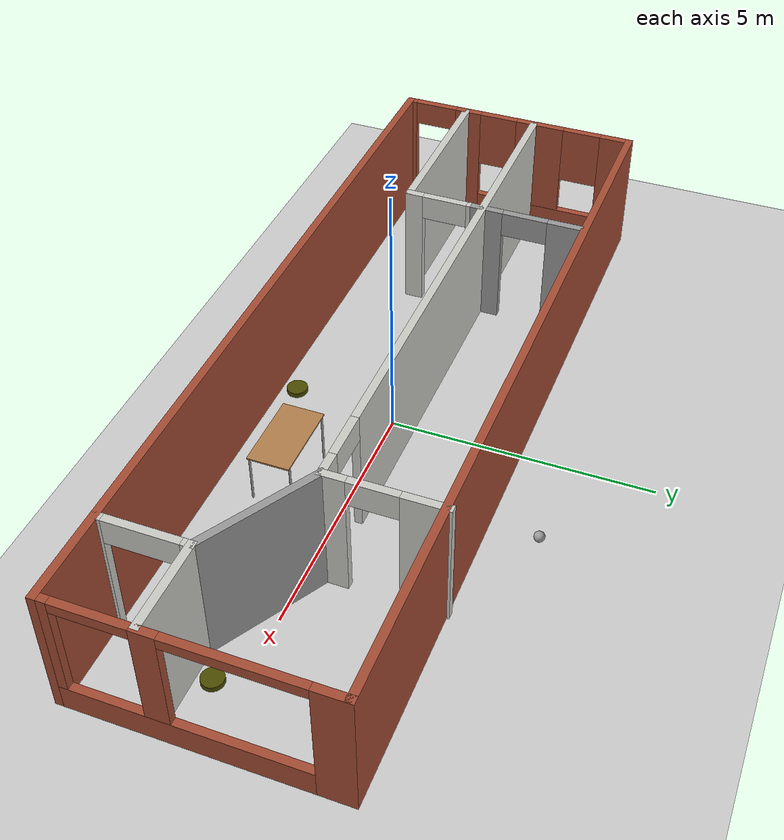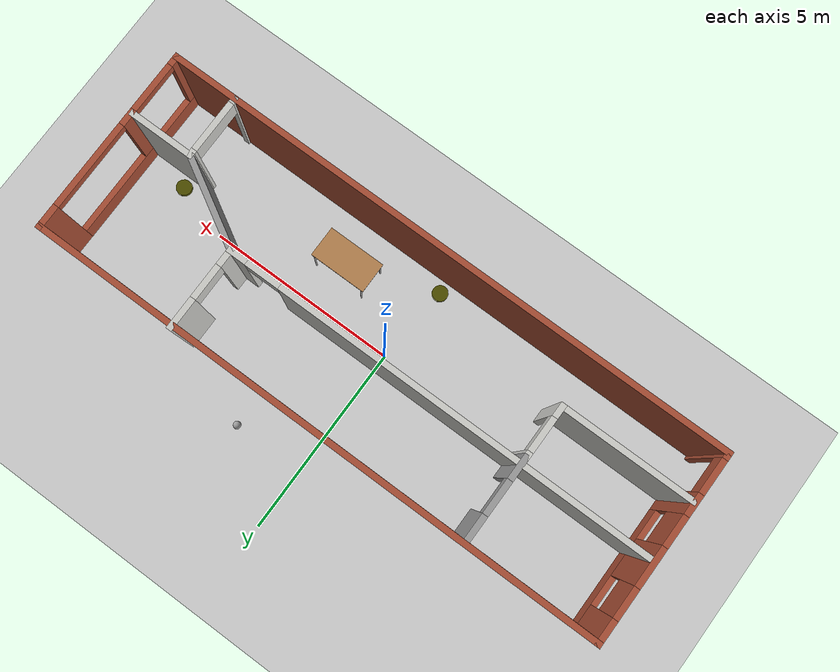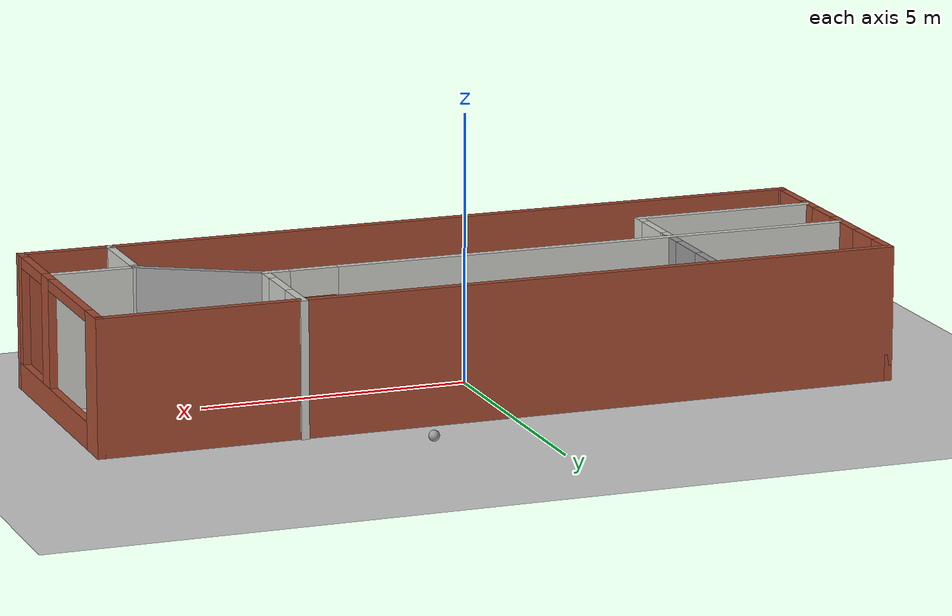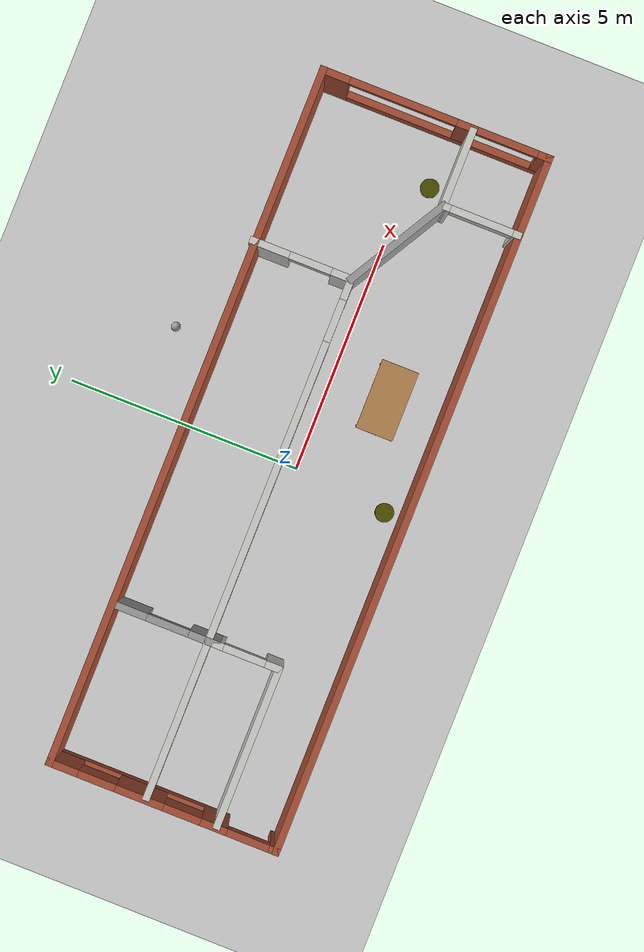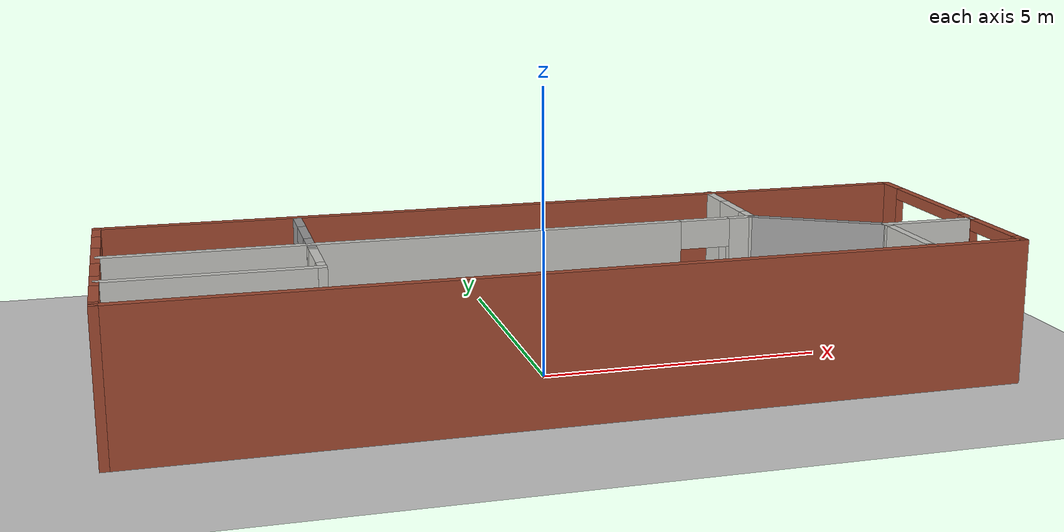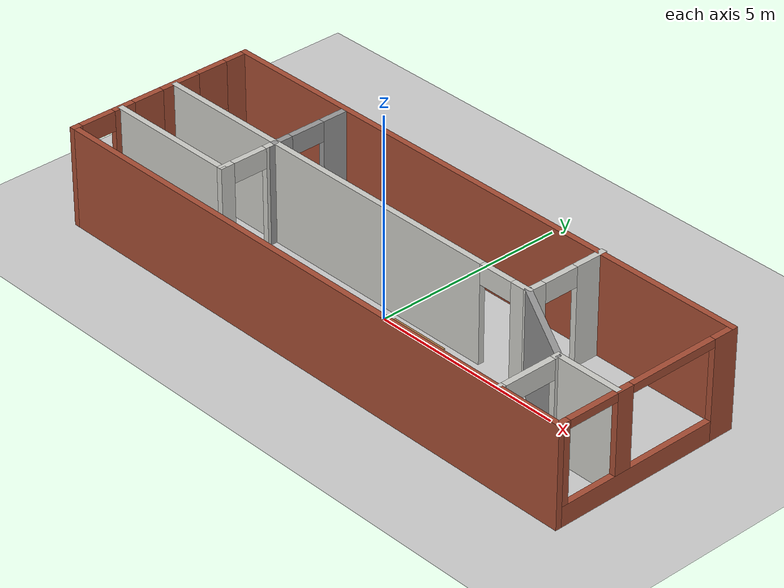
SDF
<sdf version="1.6">
 <world name="default">
  <plugin name="welcome" filename="libwelcome.so"/>
  <light name="sun" type="directional">
   <pose>0 0 10 0 -0 0</pose>
   <diffuse>0.8 0.8 0.8 1</diffuse>
   <specular>0.2 0.2 0.2 1</specular>
   <attenuation>
    <range>1000</range>
    <constant>0.9</constant>
    <linear>0.01</linear>
    <quadratic>0.001</quadratic>
   </attenuation>
   <direction>-0.5 0.1 -0.9</direction>
  </light>
  <model name="ground_plane">
   <static>1</static>
   <link name="link">
    <collision name="collision">
     <geometry><plane><normal>0 0 1</normal><size>100 100</size></plane></geometry>
     <surface><friction><ode><mu>100</mu><mu2>50</mu2></ode></friction></surface>
    </collision>
    <visual name="visual">
     <cast_shadows>0</cast_shadows>
     <geometry><plane><normal>0 0 1</normal><size>100 100</size></plane></geometry>
     <material>
      <script><uri>file://media/materials/scripts/gazebo.material</uri><name>Gazebo/Grey</name></script>
     </material>
    </visual>
   </link>
  </model>
  <gravity>0 0 -9.8</gravity>
  <magnetic_field>6e-06 2.3e-05 -4.2e-05</magnetic_field>
  <atmosphere type="adiabatic"/>
  <physics name="default_physics" default="0" type="ode">
   <max_step_size>0.001</max_step_size>
   <real_time_factor>1</real_time_factor>
   <real_time_update_rate>1000</real_time_update_rate>
  </physics>
  <scene><ambient>0.4 0.4 0.4 1</ambient><background>0.7 0.7 0.7 1</background><shadows>1</shadows></scene>
  <spherical_coordinates>
   <surface_model>EARTH_WGS84</surface_model>
   <latitude_deg>0</latitude_deg>
   <longitude_deg>0</longitude_deg>
   <elevation>0</elevation>
   <heading_deg>0</heading_deg>
  </spherical_coordinates>
  <model name="table">
   <static>1</static>
   <link name="link">
    <collision name="surface">
     <pose>0 0 1 0 -0 0</pose>
     <geometry><box><size>1.5 0.8 0.03</size></box></geometry>
     <surface><friction><ode><mu>0.6</mu><mu2>0.6</mu2></ode></friction></surface>
    </collision>
    <visual name="visual1">
     <pose>0 0 1 0 -0 0</pose>
     <geometry><box><size>1.5 0.8 0.03</size></box></geometry>
     <material>
      <script><uri>file://media/materials/scripts/gazebo.material</uri><name>Gazebo/Wood</name></script>
     </material>
    </visual>
    <collision name="front_left_leg">
     <pose>0.68 0.38 0.5 0 -0 0</pose>
     <geometry><cylinder><radius>0.02</radius><length>1</length></cylinder></geometry>
    </collision>
    <visual name="front_left_leg">
     <pose>0.68 0.38 0.5 0 -0 0</pose>
     <geometry><cylinder><radius>0.02</radius><length>1</length></cylinder></geometry>
     <material>
      <script><uri>file://media/materials/scripts/gazebo.material</uri><name>Gazebo/Grey</name></script>
     </material>
    </visual>
    <collision name="front_right_leg">
     <pose>0.68 -0.38 0.5 0 -0 0</pose>
     <geometry><cylinder><radius>0.02</radius><length>1</length></cylinder></geometry>
    </collision>
    <visual name="front_right_leg">
     <pose>0.68 -0.38 0.5 0 -0 0</pose>
     <geometry><cylinder><radius>0.02</radius><length>1</length></cylinder></geometry>
     <material>
      <script><uri>file://media/materials/scripts/gazebo.material</uri><name>Gazebo/Grey</name></script>
     </material>
    </visual>
    <collision name="back_right_leg">
     <pose>-0.68 -0.38 0.5 0 -0 0</pose>
     <geometry><cylinder><radius>0.02</radius><length>1</length></cylinder></geometry>
    </collision>
    <visual name="back_right_leg">
     <pose>-0.68 -0.38 0.5 0 -0 0</pose>
     <geometry><cylinder><radius>0.02</radius><length>1</length></cylinder></geometry>
     <material>
      <script><uri>file://media/materials/scripts/gazebo.material</uri><name>Gazebo/Grey</name></script>
     </material>
    </visual>
    <collision name="back_left_leg">
     <pose>-0.68 0.38 0.5 0 -0 0</pose>
     <geometry><cylinder><radius>0.02</radius><length>1</length></cylinder></geometry>
    </collision>
    <visual name="back_left_leg">
     <pose>-0.68 0.38 0.5 0 -0 0</pose>
     <geometry><cylinder><radius>0.02</radius><length>1</length></cylinder></geometry>
     <material>
      <script><uri>file://media/materials/scripts/gazebo.material</uri><name>Gazebo/Grey</name></script>
     </material>
    </visual>
   </link>
   <pose>1.9808 -1.22058 0 0 -0 0</pose>
  </model>
  <model name="vacuumRobot">
   <link name="link_1">
    <pose>0.031819 -5.91746 0.05875 0 -0 0</pose>
    <inertial>
     <mass>1</mass>
     <inertia><ixx>0.145833</ixx><ixy>0</ixy><ixz>0</ixz><iyy>0.145833</iyy><iyz>0</iyz><izz>0.125</izz></inertia>
    </inertial>
    <visual name="visual">
     <geometry><cylinder><radius>0.2</radius><length>0.1</length></cylinder></geometry>
     <material>
      <lighting>1</lighting>
      <script><uri>file://media/materials/scripts/gazebo.material</uri><name>Gazebo/Grey</name></script>
      <shader type="pixel"><normal_map>__default__</normal_map></shader>
      <ambient>0.3 0.3 0 1</ambient>
      <diffuse>0.7 0.7 0.7 1</diffuse>
      <specular>0.01 0.01 0.01 1</specular>
      <emissive>0 0 0 1</emissive>
     </material>
    </visual>
    <collision name="collision">
     <geometry><cylinder><radius>0.2</radius><length>0.1</length></cylinder></geometry>
     <surface>
      <friction>
       <ode><mu>1</mu><mu2>1</mu2><fdir1>0 0 0</fdir1><slip1>0</slip1><slip2>0</slip2></ode>
       <torsional>
        <coefficient>1</coefficient>
        <patch_radius>0</patch_radius>
        <surface_radius>0</surface_radius>
        <use_patch_radius>1</use_patch_radius>
        <ode><slip>0</slip></ode>
       </torsional>
      </friction>
      <bounce><restitution_coefficient>0</restitution_coefficient><threshold>1e+06</threshold></bounce>
      <contact>
       <collide_without_contact>0</collide_without_contact>
       <collide_without_contact_bitmask>1</collide_without_contact_bitmask>
       <collide_bitmask>1</collide_bitmask>
       <ode>
        <soft_cfm>0</soft_cfm>
        <soft_erp>0.2</soft_erp>
        <kp>1e+13</kp>
        <kd>1</kd>
        <max_vel>0.01</max_vel>
        <min_depth>0</min_depth>
       </ode>
       <bullet>
        <split_impulse>1</split_impulse>
        <split_impulse_penetration_threshold>-0.01</split_impulse_penetration_threshold>
        <soft_cfm>0</soft_cfm>
        <soft_erp>0.2</soft_erp>
        <kp>1e+13</kp>
        <kd>1</kd>
       </bullet>
      </contact>
     </surface>
    </collision>
   </link>
   <link name="link_2">
    <pose>0.201819 -5.91746 0.03875 0 -0 0</pose>
    <inertial>
     <mass>1</mass>
     <inertia><ixx>0.145833</ixx><ixy>0</ixy><ixz>0</ixz><iyy>0.145833</iyy><iyz>0</iyz><izz>0.125</izz></inertia>
    </inertial>
    <visual name="visual">
     <pose>0 0 0 1.5707 0 1.5707</pose>
     <geometry><cylinder><radius>0.04</radius><length>0.01</length></cylinder></geometry>
     <material>
      <lighting>1</lighting>
      <script><uri>file://media/materials/scripts/gazebo.material</uri><name>Gazebo/Grey</name></script>
      <shader type="pixel"><normal_map>__default__</normal_map></shader>
      <ambient>0.3 0.3 0.3 1</ambient>
      <diffuse>0.7 0.7 0.7 1</diffuse>
      <specular>0.01 0.01 0.01 1</specular>
      <emissive>0 0 0 1</emissive>
     </material>
    </visual>
    <collision name="collision">
     <pose>0 0 0 1.5707 0 1.5707</pose>
     <geometry><cylinder><radius>0.04</radius><length>0.01</length></cylinder></geometry>
     <surface>
      <friction>
       <ode><mu>1</mu><mu2>1</mu2><fdir1>0 0 0</fdir1><slip1>0</slip1><slip2>0</slip2></ode>
       <torsional>
        <coefficient>1</coefficient>
        <patch_radius>0</patch_radius>
        <surface_radius>0</surface_radius>
        <use_patch_radius>1</use_patch_radius>
        <ode><slip>0</slip></ode>
       </torsional>
      </friction>
      <bounce><restitution_coefficient>0</restitution_coefficient><threshold>1e+06</threshold></bounce>
      <contact>
       <collide_without_contact>0</collide_without_contact>
       <collide_without_contact_bitmask>1</collide_without_contact_bitmask>
       <collide_bitmask>1</collide_bitmask>
       <ode>
        <soft_cfm>0</soft_cfm>
        <soft_erp>0.2</soft_erp>
        <kp>1e+13</kp>
        <kd>1</kd>
        <max_vel>0.01</max_vel>
        <min_depth>0</min_depth>
       </ode>
       <bullet>
        <split_impulse>1</split_impulse>
        <split_impulse_penetration_threshold>-0.01</split_impulse_penetration_threshold>
        <soft_cfm>0</soft_cfm>
        <soft_erp>0.2</soft_erp>
        <kp>1e+13</kp>
        <kd>1</kd>
       </bullet>
      </contact>
     </surface>
    </collision>
   </link>
   <link name="link_2_clone">
    <pose>-0.138181 -5.91746 0.03875 0 -0 0</pose>
    <inertial>
     <mass>1</mass>
     <inertia><ixx>0.145833</ixx><ixy>0</ixy><ixz>0</ixz><iyy>0.145833</iyy><iyz>0</iyz><izz>0.125</izz></inertia>
    </inertial>
    <visual name="visual">
     <pose>0 0 0 1.5707 0 1.5707</pose>
     <geometry><cylinder><radius>0.04</radius><length>0.01</length></cylinder></geometry>
     <material>
      <lighting>1</lighting>
      <script><uri>file://media/materials/scripts/gazebo.material</uri><name>Gazebo/Grey</name></script>
      <shader type="pixel"><normal_map>__default__</normal_map></shader>
      <ambient>0.3 0.3 0.3 1</ambient>
      <diffuse>0.7 0.7 0.7 1</diffuse>
      <specular>0.01 0.01 0.01 1</specular>
      <emissive>0 0 0 1</emissive>
     </material>
    </visual>
    <collision name="collision">
     <pose>0 0 0 1.5707 0 1.5707</pose>
     <geometry><cylinder><radius>0.04</radius><length>0.01</length></cylinder></geometry>
     <surface>
      <friction>
       <ode><mu>1</mu><mu2>1</mu2><fdir1>0 0 0</fdir1><slip1>0</slip1><slip2>0</slip2></ode>
       <torsional>
        <coefficient>1</coefficient>
        <patch_radius>0</patch_radius>
        <surface_radius>0</surface_radius>
        <use_patch_radius>1</use_patch_radius>
        <ode><slip>0</slip></ode>
       </torsional>
      </friction>
      <bounce><restitution_coefficient>0</restitution_coefficient><threshold>1e+06</threshold></bounce>
      <contact>
       <collide_without_contact>0</collide_without_contact>
       <collide_without_contact_bitmask>1</collide_without_contact_bitmask>
       <collide_bitmask>1</collide_bitmask>
       <ode>
        <soft_cfm>0</soft_cfm>
        <soft_erp>0.2</soft_erp>
        <kp>1e+13</kp>
        <kd>1</kd>
        <max_vel>0.01</max_vel>
        <min_depth>0</min_depth>
       </ode>
       <bullet>
        <split_impulse>1</split_impulse>
        <split_impulse_penetration_threshold>-0.01</split_impulse_penetration_threshold>
        <soft_cfm>0</soft_cfm>
        <soft_erp>0.2</soft_erp>
        <kp>1e+13</kp>
        <kd>1</kd>
       </bullet>
      </contact>
     </surface>
    </collision>
   </link>
   <link name="link_3">
    <pose>0.031819 -5.74746 0.005 0 -0 0</pose>
    <inertial>
     <mass>1</mass>
     <inertia><ixx>0.1</ixx><ixy>0</ixy><ixz>0</ixz><iyy>0.1</iyy><iyz>0</iyz><izz>0.1</izz></inertia>
    </inertial>
    <visual name="visual">
     <geometry><sphere><radius>0.01</radius></sphere></geometry>
     <material>
      <lighting>1</lighting>
      <script><uri>file://media/materials/scripts/gazebo.material</uri><name>Gazebo/Grey</name></script>
      <shader type="pixel"><normal_map>__default__</normal_map></shader>
      <ambient>0.3 0.3 0.3 1</ambient>
      <diffuse>0.7 0.7 0.7 1</diffuse>
      <specular>0.01 0.01 0.01 1</specular>
      <emissive>0 0 0 1</emissive>
     </material>
    </visual>
    <collision name="collision">
     <geometry><sphere><radius>0.01</radius></sphere></geometry>
     <surface>
      <friction>
       <ode><mu>1</mu><mu2>1</mu2><fdir1>0 0 0</fdir1><slip1>0</slip1><slip2>0</slip2></ode>
       <torsional>
        <coefficient>1</coefficient>
        <patch_radius>0</patch_radius>
        <surface_radius>0</surface_radius>
        <use_patch_radius>1</use_patch_radius>
        <ode><slip>0</slip></ode>
       </torsional>
      </friction>
      <bounce><restitution_coefficient>0</restitution_coefficient><threshold>1e+06</threshold></bounce>
      <contact>
       <collide_without_contact>0</collide_without_contact>
       <collide_without_contact_bitmask>1</collide_without_contact_bitmask>
       <collide_bitmask>1</collide_bitmask>
       <ode>
        <soft_cfm>0</soft_cfm>
        <soft_erp>0.2</soft_erp>
        <kp>1e+13</kp>
        <kd>1</kd>
        <max_vel>0.01</max_vel>
        <min_depth>0</min_depth>
       </ode>
       <bullet>
        <split_impulse>1</split_impulse>
        <split_impulse_penetration_threshold>-0.01</split_impulse_penetration_threshold>
        <soft_cfm>0</soft_cfm>
        <soft_erp>0.2</soft_erp>
        <kp>1e+13</kp>
        <kd>1</kd>
       </bullet>
      </contact>
     </surface>
    </collision>
   </link>
   <joint name="link_1_JOINT_4" type="revolute">
    <parent>link_1</parent>
    <child>link_2</child>
    <axis>
     <xyz>1 0 0</xyz>
     <use_parent_model_frame>0</use_parent_model_frame>
     <limit>
      <lower>-1.79769e+308</lower>
      <upper>1.79769e+308</upper>
      <effort>-1</effort>
      <velocity>-1</velocity>
     </limit>
     <dynamics>
      <spring_reference>0</spring_reference>
      <spring_stiffness>0</spring_stiffness>
      <damping>0</damping>
      <friction>0</friction>
     </dynamics>
    </axis>
    <physics>
     <ode><limit><cfm>0</cfm><erp>0.2</erp></limit><suspension><cfm>0</cfm><erp>0.2</erp></suspension></ode>
    </physics>
   </joint>
   <joint name="link_1_JOINT_5" type="revolute">
    <parent>link_1</parent>
    <child>link_2_clone</child>
    <axis>
     <xyz>1 0 0</xyz>
     <use_parent_model_frame>0</use_parent_model_frame>
     <limit>
      <lower>-1.79769e+308</lower>
      <upper>1.79769e+308</upper>
      <effort>-1</effort>
      <velocity>-1</velocity>
     </limit>
     <dynamics>
      <spring_reference>0</spring_reference>
      <spring_stiffness>0</spring_stiffness>
      <damping>0</damping>
      <friction>0</friction>
     </dynamics>
    </axis>
    <physics>
     <ode><limit><cfm>0</cfm><erp>0.2</erp></limit><suspension><cfm>0</cfm><erp>0.2</erp></suspension></ode>
    </physics>
   </joint>
   <joint name="link_1_JOINT_6" type="revolute">
    <parent>link_1</parent>
    <child>link_3</child>
    <axis>
     <xyz>0 0 1</xyz>
     <use_parent_model_frame>0</use_parent_model_frame>
     <limit>
      <lower>-1.79769e+308</lower>
      <upper>1.79769e+308</upper>
      <effort>-1</effort>
      <velocity>-1</velocity>
     </limit>
     <dynamics>
      <spring_reference>0</spring_reference>
      <spring_stiffness>0</spring_stiffness>
      <damping>0</damping>
      <friction>0</friction>
     </dynamics>
    </axis>
    <physics>
     <ode><limit><cfm>0</cfm><erp>0.2</erp></limit><suspension><cfm>0</cfm><erp>0.2</erp></suspension></ode>
    </physics>
   </joint>
   <static>0</static>
   <pose>6.41807 5.47321 0.131505 0.022012 -2e-06 -0.000739</pose>
  </model>
  <model name="vacuumRobot_clone">
   <link name="link_1">
    <pose>0.031819 -5.91746 0.05875 0 -0 0</pose>
    <inertial>
     <mass>1</mass>
     <inertia><ixx>0.145833</ixx><ixy>0</ixy><ixz>0</ixz><iyy>0.145833</iyy><iyz>0</iyz><izz>0.125</izz></inertia>
    </inertial>
    <visual name="visual">
     <geometry><cylinder><radius>0.2</radius><length>0.1</length></cylinder></geometry>
     <material>
      <lighting>1</lighting>
      <script><uri>file://media/materials/scripts/gazebo.material</uri><name>Gazebo/Grey</name></script>
      <shader type="pixel"><normal_map>__default__</normal_map></shader>
      <ambient>0.3 0.3 0 1</ambient>
      <diffuse>0.7 0.7 0.7 1</diffuse>
      <specular>0.01 0.01 0.01 1</specular>
      <emissive>0 0 0 1</emissive>
     </material>
    </visual>
    <collision name="collision">
     <geometry><cylinder><radius>0.2</radius><length>0.1</length></cylinder></geometry>
     <surface>
      <friction>
       <ode><mu>1</mu><mu2>1</mu2><fdir1>0 0 0</fdir1><slip1>0</slip1><slip2>0</slip2></ode>
       <torsional>
        <coefficient>1</coefficient>
        <patch_radius>0</patch_radius>
        <surface_radius>0</surface_radius>
        <use_patch_radius>1</use_patch_radius>
        <ode><slip>0</slip></ode>
       </torsional>
      </friction>
      <bounce><restitution_coefficient>0</restitution_coefficient><threshold>1e+06</threshold></bounce>
      <contact>
       <collide_without_contact>0</collide_without_contact>
       <collide_without_contact_bitmask>1</collide_without_contact_bitmask>
       <collide_bitmask>1</collide_bitmask>
       <ode>
        <soft_cfm>0</soft_cfm>
        <soft_erp>0.2</soft_erp>
        <kp>1e+13</kp>
        <kd>1</kd>
        <max_vel>0.01</max_vel>
        <min_depth>0</min_depth>
       </ode>
       <bullet>
        <split_impulse>1</split_impulse>
        <split_impulse_penetration_threshold>-0.01</split_impulse_penetration_threshold>
        <soft_cfm>0</soft_cfm>
        <soft_erp>0.2</soft_erp>
        <kp>1e+13</kp>
        <kd>1</kd>
       </bullet>
      </contact>
     </surface>
    </collision>
   </link>
   <link name="link_2">
    <pose>0.201819 -5.91746 0.03875 0 -0 0</pose>
    <inertial>
     <mass>1</mass>
     <inertia><ixx>0.145833</ixx><ixy>0</ixy><ixz>0</ixz><iyy>0.145833</iyy><iyz>0</iyz><izz>0.125</izz></inertia>
    </inertial>
    <visual name="visual">
     <pose>0 0 0 1.5707 0 1.5707</pose>
     <geometry><cylinder><radius>0.04</radius><length>0.01</length></cylinder></geometry>
     <material>
      <lighting>1</lighting>
      <script><uri>file://media/materials/scripts/gazebo.material</uri><name>Gazebo/Grey</name></script>
      <shader type="pixel"><normal_map>__default__</normal_map></shader>
      <ambient>0.3 0.3 0.3 1</ambient>
      <diffuse>0.7 0.7 0.7 1</diffuse>
      <specular>0.01 0.01 0.01 1</specular>
      <emissive>0 0 0 1</emissive>
     </material>
    </visual>
    <collision name="collision">
     <pose>0 0 0 1.5707 0 1.5707</pose>
     <geometry><cylinder><radius>0.04</radius><length>0.01</length></cylinder></geometry>
     <surface>
      <friction>
       <ode><mu>1</mu><mu2>1</mu2><fdir1>0 0 0</fdir1><slip1>0</slip1><slip2>0</slip2></ode>
       <torsional>
        <coefficient>1</coefficient>
        <patch_radius>0</patch_radius>
        <surface_radius>0</surface_radius>
        <use_patch_radius>1</use_patch_radius>
        <ode><slip>0</slip></ode>
       </torsional>
      </friction>
      <bounce><restitution_coefficient>0</restitution_coefficient><threshold>1e+06</threshold></bounce>
      <contact>
       <collide_without_contact>0</collide_without_contact>
       <collide_without_contact_bitmask>1</collide_without_contact_bitmask>
       <collide_bitmask>1</collide_bitmask>
       <ode>
        <soft_cfm>0</soft_cfm>
        <soft_erp>0.2</soft_erp>
        <kp>1e+13</kp>
        <kd>1</kd>
        <max_vel>0.01</max_vel>
        <min_depth>0</min_depth>
       </ode>
       <bullet>
        <split_impulse>1</split_impulse>
        <split_impulse_penetration_threshold>-0.01</split_impulse_penetration_threshold>
        <soft_cfm>0</soft_cfm>
        <soft_erp>0.2</soft_erp>
        <kp>1e+13</kp>
        <kd>1</kd>
       </bullet>
      </contact>
     </surface>
    </collision>
   </link>
   <link name="link_2_clone">
    <pose>-0.138181 -5.91746 0.03875 0 -0 0</pose>
    <inertial>
     <mass>1</mass>
     <inertia><ixx>0.145833</ixx><ixy>0</ixy><ixz>0</ixz><iyy>0.145833</iyy><iyz>0</iyz><izz>0.125</izz></inertia>
    </inertial>
    <visual name="visual">
     <pose>0 0 0 1.5707 0 1.5707</pose>
     <geometry><cylinder><radius>0.04</radius><length>0.01</length></cylinder></geometry>
     <material>
      <lighting>1</lighting>
      <script><uri>file://media/materials/scripts/gazebo.material</uri><name>Gazebo/Grey</name></script>
      <shader type="pixel"><normal_map>__default__</normal_map></shader>
      <ambient>0.3 0.3 0.3 1</ambient>
      <diffuse>0.7 0.7 0.7 1</diffuse>
      <specular>0.01 0.01 0.01 1</specular>
      <emissive>0 0 0 1</emissive>
     </material>
    </visual>
    <collision name="collision">
     <pose>0 0 0 1.5707 0 1.5707</pose>
     <geometry><cylinder><radius>0.04</radius><length>0.01</length></cylinder></geometry>
     <surface>
      <friction>
       <ode><mu>1</mu><mu2>1</mu2><fdir1>0 0 0</fdir1><slip1>0</slip1><slip2>0</slip2></ode>
       <torsional>
        <coefficient>1</coefficient>
        <patch_radius>0</patch_radius>
        <surface_radius>0</surface_radius>
        <use_patch_radius>1</use_patch_radius>
        <ode><slip>0</slip></ode>
       </torsional>
      </friction>
      <bounce><restitution_coefficient>0</restitution_coefficient><threshold>1e+06</threshold></bounce>
      <contact>
       <collide_without_contact>0</collide_without_contact>
       <collide_without_contact_bitmask>1</collide_without_contact_bitmask>
       <collide_bitmask>1</collide_bitmask>
       <ode>
        <soft_cfm>0</soft_cfm>
        <soft_erp>0.2</soft_erp>
        <kp>1e+13</kp>
        <kd>1</kd>
        <max_vel>0.01</max_vel>
        <min_depth>0</min_depth>
       </ode>
       <bullet>
        <split_impulse>1</split_impulse>
        <split_impulse_penetration_threshold>-0.01</split_impulse_penetration_threshold>
        <soft_cfm>0</soft_cfm>
        <soft_erp>0.2</soft_erp>
        <kp>1e+13</kp>
        <kd>1</kd>
       </bullet>
      </contact>
     </surface>
    </collision>
   </link>
   <link name="link_3">
    <pose>0.031819 -5.74746 0.005 0 -0 0</pose>
    <inertial>
     <mass>1</mass>
     <inertia><ixx>0.1</ixx><ixy>0</ixy><ixz>0</ixz><iyy>0.1</iyy><iyz>0</iyz><izz>0.1</izz></inertia>
    </inertial>
    <visual name="visual">
     <geometry><sphere><radius>0.01</radius></sphere></geometry>
     <material>
      <lighting>1</lighting>
      <script><uri>file://media/materials/scripts/gazebo.material</uri><name>Gazebo/Grey</name></script>
      <shader type="pixel"><normal_map>__default__</normal_map></shader>
      <ambient>0.3 0.3 0.3 1</ambient>
      <diffuse>0.7 0.7 0.7 1</diffuse>
      <specular>0.01 0.01 0.01 1</specular>
      <emissive>0 0 0 1</emissive>
     </material>
    </visual>
    <collision name="collision">
     <geometry><sphere><radius>0.01</radius></sphere></geometry>
     <surface>
      <friction>
       <ode><mu>1</mu><mu2>1</mu2><fdir1>0 0 0</fdir1><slip1>0</slip1><slip2>0</slip2></ode>
       <torsional>
        <coefficient>1</coefficient>
        <patch_radius>0</patch_radius>
        <surface_radius>0</surface_radius>
        <use_patch_radius>1</use_patch_radius>
        <ode><slip>0</slip></ode>
       </torsional>
      </friction>
      <bounce><restitution_coefficient>0</restitution_coefficient><threshold>1e+06</threshold></bounce>
      <contact>
       <collide_without_contact>0</collide_without_contact>
       <collide_without_contact_bitmask>1</collide_without_contact_bitmask>
       <collide_bitmask>1</collide_bitmask>
       <ode>
        <soft_cfm>0</soft_cfm>
        <soft_erp>0.2</soft_erp>
        <kp>1e+13</kp>
        <kd>1</kd>
        <max_vel>0.01</max_vel>
        <min_depth>0</min_depth>
       </ode>
       <bullet>
        <split_impulse>1</split_impulse>
        <split_impulse_penetration_threshold>-0.01</split_impulse_penetration_threshold>
        <soft_cfm>0</soft_cfm>
        <soft_erp>0.2</soft_erp>
        <kp>1e+13</kp>
        <kd>1</kd>
       </bullet>
      </contact>
     </surface>
    </collision>
   </link>
   <joint name="link_1_JOINT_4" type="revolute">
    <parent>link_1</parent>
    <child>link_2</child>
    <axis>
     <xyz>1 0 0</xyz>
     <use_parent_model_frame>0</use_parent_model_frame>
     <limit>
      <lower>-1.79769e+308</lower>
      <upper>1.79769e+308</upper>
      <effort>-1</effort>
      <velocity>-1</velocity>
     </limit>
     <dynamics>
      <spring_reference>0</spring_reference>
      <spring_stiffness>0</spring_stiffness>
      <damping>0</damping>
      <friction>0</friction>
     </dynamics>
    </axis>
    <physics>
     <ode><limit><cfm>0</cfm><erp>0.2</erp></limit><suspension><cfm>0</cfm><erp>0.2</erp></suspension></ode>
    </physics>
   </joint>
   <joint name="link_1_JOINT_5" type="revolute">
    <parent>link_1</parent>
    <child>link_2_clone</child>
    <axis>
     <xyz>1 0 0</xyz>
     <use_parent_model_frame>0</use_parent_model_frame>
     <limit>
      <lower>-1.79769e+308</lower>
      <upper>1.79769e+308</upper>
      <effort>-1</effort>
      <velocity>-1</velocity>
     </limit>
     <dynamics>
      <spring_reference>0</spring_reference>
      <spring_stiffness>0</spring_stiffness>
      <damping>0</damping>
      <friction>0</friction>
     </dynamics>
    </axis>
    <physics>
     <ode><limit><cfm>0</cfm><erp>0.2</erp></limit><suspension><cfm>0</cfm><erp>0.2</erp></suspension></ode>
    </physics>
   </joint>
   <joint name="link_1_JOINT_6" type="revolute">
    <parent>link_1</parent>
    <child>link_3</child>
    <axis>
     <xyz>0 0 1</xyz>
     <use_parent_model_frame>0</use_parent_model_frame>
     <limit>
      <lower>-1.79769e+308</lower>
      <upper>1.79769e+308</upper>
      <effort>-1</effort>
      <velocity>-1</velocity>
     </limit>
     <dynamics>
      <spring_reference>0</spring_reference>
      <spring_stiffness>0</spring_stiffness>
      <damping>0</damping>
      <friction>0</friction>
     </dynamics>
    </axis>
    <physics>
     <ode><limit><cfm>0</cfm><erp>0.2</erp></limit><suspension><cfm>0</cfm><erp>0.2</erp></suspension></ode>
    </physics>
   </joint>
   <static>0</static>
   <pose>-0.205057 3.87634 0.131505 0.022012 -2e-06 -0.000765</pose>
  </model>
  <model name="buildingMyHouse">
   <link name="Wall_33">
    <pose>0 -2.44789 0 0 -0 3.14159</pose>
    <visual name="Wall_33_Visual">
     <pose>0 0 1.25 0 -0 0</pose>
     <geometry><box><size>15 0.15 2.5</size></box></geometry>
     <material>
      <script><uri>file://media/materials/scripts/gazebo.material</uri><name>Gazebo/Bricks</name></script>
      <ambient>1 1 1 1</ambient>
      <shader type="pixel"/>
      <diffuse>1 1 1 1</diffuse>
      <specular>0.2 0.2 0.2 1</specular>
      <emissive>0 0 0 1</emissive>
     </material>
     <meta><layer>0</layer></meta>
    </visual>
    <collision name="Wall_33_Collision">
     <pose>0 0 1.25 0 -0 0</pose>
     <geometry><box><size>15 0.15 2.5</size></box></geometry>
     <surface>
      <friction>
       <ode><mu>1</mu><mu2>1</mu2><fdir1>0 0 0</fdir1><slip1>0</slip1><slip2>0</slip2></ode>
       <torsional>
        <coefficient>1</coefficient>
        <patch_radius>0</patch_radius>
        <surface_radius>0</surface_radius>
        <use_patch_radius>1</use_patch_radius>
        <ode><slip>0</slip></ode>
       </torsional>
      </friction>
      <bounce><restitution_coefficient>0</restitution_coefficient><threshold>1e+06</threshold></bounce>
      <contact>
       <collide_without_contact>0</collide_without_contact>
       <collide_without_contact_bitmask>1</collide_without_contact_bitmask>
       <collide_bitmask>1</collide_bitmask>
       <ode>
        <soft_cfm>0</soft_cfm>
        <soft_erp>0.2</soft_erp>
        <kp>1e+13</kp>
        <kd>1</kd>
        <max_vel>0.01</max_vel>
        <min_depth>0</min_depth>
       </ode>
       <bullet>
        <split_impulse>1</split_impulse>
        <split_impulse_penetration_threshold>-0.01</split_impulse_penetration_threshold>
        <soft_cfm>0</soft_cfm>
        <soft_erp>0.2</soft_erp>
        <kp>1e+13</kp>
        <kd>1</kd>
       </bullet>
      </contact>
     </surface>
    </collision>
   </link>
   <link name="Wall_34">
    <pose>-7.425 -0.022893 0 0 -0 1.5708</pose>
    <visual name="Wall_34_Visual_0">
     <pose>-2.38147 0 1.25 0 -0 0</pose>
     <geometry><box><size>0.237054 0.15 2.5</size></box></geometry>
     <material>
      <script><uri>file://media/materials/scripts/gazebo.material</uri><name>Gazebo/Bricks</name></script>
      <ambient>1 1 1 1</ambient>
      <shader type="pixel"/>
      <diffuse>1 1 1 1</diffuse>
      <specular>0.2 0.2 0.2 1</specular>
      <emissive>0 0 0 1</emissive>
     </material>
     <meta><layer>0</layer></meta>
    </visual>
    <visual name="Wall_34_Visual_1">
     <pose>-1.08246 0 1.25 0 -0 0</pose>
     <geometry><box><size>0.560967 0.15 2.5</size></box></geometry>
     <material>
      <script><uri>file://media/materials/scripts/gazebo.material</uri><name>Gazebo/Bricks</name></script>
      <ambient>1 1 1 1</ambient>
      <shader type="pixel"/>
      <diffuse>1 1 1 1</diffuse>
      <specular>0.2 0.2 0.2 1</specular>
      <emissive>0 0 0 1</emissive>
     </material>
     <meta><layer>0</layer></meta>
    </visual>
    <visual name="Wall_34_Visual_2">
     <pose>0.849011 0 0.25 0 -0 0</pose>
     <geometry><box><size>3.30198 0.15 0.5</size></box></geometry>
     <material>
      <script><uri>file://media/materials/scripts/gazebo.material</uri><name>Gazebo/Bricks</name></script>
      <ambient>1 1 1 1</ambient>
      <shader type="pixel"/>
      <diffuse>1 1 1 1</diffuse>
      <specular>0.2 0.2 0.2 1</specular>
      <emissive>0 0 0 1</emissive>
     </material>
     <meta><layer>0</layer></meta>
    </visual>
    <visual name="Wall_34_Visual_3">
     <pose>0.51168 0 1.5 0 -0 0</pose>
     <geometry><box><size>1.02732 0.15 2</size></box></geometry>
     <material>
      <script><uri>file://media/materials/scripts/gazebo.material</uri><name>Gazebo/Bricks</name></script>
      <ambient>1 1 1 1</ambient>
      <shader type="pixel"/>
      <diffuse>1 1 1 1</diffuse>
      <specular>0.2 0.2 0.2 1</specular>
      <emissive>0 0 0 1</emissive>
     </material>
     <meta><layer>0</layer></meta>
    </visual>
    <visual name="Wall_34_Visual_4">
     <pose>2.16267 0 1.5 0 -0 0</pose>
     <geometry><box><size>0.674661 0.15 2</size></box></geometry>
     <material>
      <script><uri>file://media/materials/scripts/gazebo.material</uri><name>Gazebo/Bricks</name></script>
      <ambient>1 1 1 1</ambient>
      <shader type="pixel"/>
      <diffuse>1 1 1 1</diffuse>
      <specular>0.2 0.2 0.2 1</specular>
      <emissive>0 0 0 1</emissive>
     </material>
     <meta><layer>0</layer></meta>
    </visual>
    <visual name="Wall_34_Visual_5">
     <pose>-0.401979 0 1.9 0 -0 0</pose>
     <geometry><box><size>0.8 0.15 1.2</size></box></geometry>
     <material>
      <script><uri>file://media/materials/scripts/gazebo.material</uri><name>Gazebo/Bricks</name></script>
      <ambient>1 1 1 1</ambient>
      <shader type="pixel"/>
      <diffuse>1 1 1 1</diffuse>
      <specular>0.2 0.2 0.2 1</specular>
      <emissive>0 0 0 1</emissive>
     </material>
     <meta><layer>0</layer></meta>
    </visual>
    <visual name="Wall_34_Visual_6">
     <pose>1.42534 0 1.9 0 -0 0</pose>
     <geometry><box><size>0.8 0.15 1.2</size></box></geometry>
     <material>
      <script><uri>file://media/materials/scripts/gazebo.material</uri><name>Gazebo/Bricks</name></script>
      <ambient>1 1 1 1</ambient>
      <shader type="pixel"/>
      <diffuse>1 1 1 1</diffuse>
      <specular>0.2 0.2 0.2 1</specular>
      <emissive>0 0 0 1</emissive>
     </material>
     <meta><layer>0</layer></meta>
    </visual>
    <visual name="Wall_34_Visual_7">
     <pose>-1.81295 0 2.25 0 -0 0</pose>
     <geometry><box><size>0.9 0.15 0.5</size></box></geometry>
     <material>
      <script><uri>file://media/materials/scripts/gazebo.material</uri><name>Gazebo/Bricks</name></script>
      <ambient>1 1 1 1</ambient>
      <shader type="pixel"/>
      <diffuse>1 1 1 1</diffuse>
      <specular>0.2 0.2 0.2 1</specular>
      <emissive>0 0 0 1</emissive>
     </material>
     <meta><layer>0</layer></meta>
    </visual>
    <collision name="Wall_34_Collision_0">
     <pose>-2.38147 0 1.25 0 -0 0</pose>
     <geometry><box><size>0.237054 0.15 2.5</size></box></geometry>
     <surface>
      <friction>
       <ode><mu>1</mu><mu2>1</mu2><fdir1>0 0 0</fdir1><slip1>0</slip1><slip2>0</slip2></ode>
       <torsional>
        <coefficient>1</coefficient>
        <patch_radius>0</patch_radius>
        <surface_radius>0</surface_radius>
        <use_patch_radius>1</use_patch_radius>
        <ode><slip>0</slip></ode>
       </torsional>
      </friction>
      <bounce><restitution_coefficient>0</restitution_coefficient><threshold>1e+06</threshold></bounce>
      <contact>
       <collide_without_contact>0</collide_without_contact>
       <collide_without_contact_bitmask>1</collide_without_contact_bitmask>
       <collide_bitmask>1</collide_bitmask>
       <ode>
        <soft_cfm>0</soft_cfm>
        <soft_erp>0.2</soft_erp>
        <kp>1e+13</kp>
        <kd>1</kd>
        <max_vel>0.01</max_vel>
        <min_depth>0</min_depth>
       </ode>
       <bullet>
        <split_impulse>1</split_impulse>
        <split_impulse_penetration_threshold>-0.01</split_impulse_penetration_threshold>
        <soft_cfm>0</soft_cfm>
        <soft_erp>0.2</soft_erp>
        <kp>1e+13</kp>
        <kd>1</kd>
       </bullet>
      </contact>
     </surface>
    </collision>
    <collision name="Wall_34_Collision_1">
     <pose>-1.08246 0 1.25 0 -0 0</pose>
     <geometry><box><size>0.560967 0.15 2.5</size></box></geometry>
     <surface>
      <friction>
       <ode><mu>1</mu><mu2>1</mu2><fdir1>0 0 0</fdir1><slip1>0</slip1><slip2>0</slip2></ode>
       <torsional>
        <coefficient>1</coefficient>
        <patch_radius>0</patch_radius>
        <surface_radius>0</surface_radius>
        <use_patch_radius>1</use_patch_radius>
        <ode><slip>0</slip></ode>
       </torsional>
      </friction>
      <bounce><restitution_coefficient>0</restitution_coefficient><threshold>1e+06</threshold></bounce>
      <contact>
       <collide_without_contact>0</collide_without_contact>
       <collide_without_contact_bitmask>1</collide_without_contact_bitmask>
       <collide_bitmask>1</collide_bitmask>
       <ode>
        <soft_cfm>0</soft_cfm>
        <soft_erp>0.2</soft_erp>
        <kp>1e+13</kp>
        <kd>1</kd>
        <max_vel>0.01</max_vel>
        <min_depth>0</min_depth>
       </ode>
       <bullet>
        <split_impulse>1</split_impulse>
        <split_impulse_penetration_threshold>-0.01</split_impulse_penetration_threshold>
        <soft_cfm>0</soft_cfm>
        <soft_erp>0.2</soft_erp>
        <kp>1e+13</kp>
        <kd>1</kd>
       </bullet>
      </contact>
     </surface>
    </collision>
    <collision name="Wall_34_Collision_2">
     <pose>0.849011 0 0.25 0 -0 0</pose>
     <geometry><box><size>3.30198 0.15 0.5</size></box></geometry>
     <surface>
      <friction>
       <ode><mu>1</mu><mu2>1</mu2><fdir1>0 0 0</fdir1><slip1>0</slip1><slip2>0</slip2></ode>
       <torsional>
        <coefficient>1</coefficient>
        <patch_radius>0</patch_radius>
        <surface_radius>0</surface_radius>
        <use_patch_radius>1</use_patch_radius>
        <ode><slip>0</slip></ode>
       </torsional>
      </friction>
      <bounce><restitution_coefficient>0</restitution_coefficient><threshold>1e+06</threshold></bounce>
      <contact>
       <collide_without_contact>0</collide_without_contact>
       <collide_without_contact_bitmask>1</collide_without_contact_bitmask>
       <collide_bitmask>1</collide_bitmask>
       <ode>
        <soft_cfm>0</soft_cfm>
        <soft_erp>0.2</soft_erp>
        <kp>1e+13</kp>
        <kd>1</kd>
        <max_vel>0.01</max_vel>
        <min_depth>0</min_depth>
       </ode>
       <bullet>
        <split_impulse>1</split_impulse>
        <split_impulse_penetration_threshold>-0.01</split_impulse_penetration_threshold>
        <soft_cfm>0</soft_cfm>
        <soft_erp>0.2</soft_erp>
        <kp>1e+13</kp>
        <kd>1</kd>
       </bullet>
      </contact>
     </surface>
    </collision>
    <collision name="Wall_34_Collision_3">
     <pose>0.51168 0 1.5 0 -0 0</pose>
     <geometry><box><size>1.02732 0.15 2</size></box></geometry>
     <surface>
      <friction>
       <ode><mu>1</mu><mu2>1</mu2><fdir1>0 0 0</fdir1><slip1>0</slip1><slip2>0</slip2></ode>
       <torsional>
        <coefficient>1</coefficient>
        <patch_radius>0</patch_radius>
        <surface_radius>0</surface_radius>
        <use_patch_radius>1</use_patch_radius>
        <ode><slip>0</slip></ode>
       </torsional>
      </friction>
      <bounce><restitution_coefficient>0</restitution_coefficient><threshold>1e+06</threshold></bounce>
      <contact>
       <collide_without_contact>0</collide_without_contact>
       <collide_without_contact_bitmask>1</collide_without_contact_bitmask>
       <collide_bitmask>1</collide_bitmask>
       <ode>
        <soft_cfm>0</soft_cfm>
        <soft_erp>0.2</soft_erp>
        <kp>1e+13</kp>
        <kd>1</kd>
        <max_vel>0.01</max_vel>
        <min_depth>0</min_depth>
       </ode>
       <bullet>
        <split_impulse>1</split_impulse>
        <split_impulse_penetration_threshold>-0.01</split_impulse_penetration_threshold>
        <soft_cfm>0</soft_cfm>
        <soft_erp>0.2</soft_erp>
        <kp>1e+13</kp>
        <kd>1</kd>
       </bullet>
      </contact>
     </surface>
    </collision>
    <collision name="Wall_34_Collision_4">
     <pose>2.16267 0 1.5 0 -0 0</pose>
     <geometry><box><size>0.674661 0.15 2</size></box></geometry>
     <surface>
      <friction>
       <ode><mu>1</mu><mu2>1</mu2><fdir1>0 0 0</fdir1><slip1>0</slip1><slip2>0</slip2></ode>
       <torsional>
        <coefficient>1</coefficient>
        <patch_radius>0</patch_radius>
        <surface_radius>0</surface_radius>
        <use_patch_radius>1</use_patch_radius>
        <ode><slip>0</slip></ode>
       </torsional>
      </friction>
      <bounce><restitution_coefficient>0</restitution_coefficient><threshold>1e+06</threshold></bounce>
      <contact>
       <collide_without_contact>0</collide_without_contact>
       <collide_without_contact_bitmask>1</collide_without_contact_bitmask>
       <collide_bitmask>1</collide_bitmask>
       <ode>
        <soft_cfm>0</soft_cfm>
        <soft_erp>0.2</soft_erp>
        <kp>1e+13</kp>
        <kd>1</kd>
        <max_vel>0.01</max_vel>
        <min_depth>0</min_depth>
       </ode>
       <bullet>
        <split_impulse>1</split_impulse>
        <split_impulse_penetration_threshold>-0.01</split_impulse_penetration_threshold>
        <soft_cfm>0</soft_cfm>
        <soft_erp>0.2</soft_erp>
        <kp>1e+13</kp>
        <kd>1</kd>
       </bullet>
      </contact>
     </surface>
    </collision>
    <collision name="Wall_34_Collision_5">
     <pose>-0.401979 0 1.9 0 -0 0</pose>
     <geometry><box><size>0.8 0.15 1.2</size></box></geometry>
     <surface>
      <friction>
       <ode><mu>1</mu><mu2>1</mu2><fdir1>0 0 0</fdir1><slip1>0</slip1><slip2>0</slip2></ode>
       <torsional>
        <coefficient>1</coefficient>
        <patch_radius>0</patch_radius>
        <surface_radius>0</surface_radius>
        <use_patch_radius>1</use_patch_radius>
        <ode><slip>0</slip></ode>
       </torsional>
      </friction>
      <bounce><restitution_coefficient>0</restitution_coefficient><threshold>1e+06</threshold></bounce>
      <contact>
       <collide_without_contact>0</collide_without_contact>
       <collide_without_contact_bitmask>1</collide_without_contact_bitmask>
       <collide_bitmask>1</collide_bitmask>
       <ode>
        <soft_cfm>0</soft_cfm>
        <soft_erp>0.2</soft_erp>
        <kp>1e+13</kp>
        <kd>1</kd>
        <max_vel>0.01</max_vel>
        <min_depth>0</min_depth>
       </ode>
       <bullet>
        <split_impulse>1</split_impulse>
        <split_impulse_penetration_threshold>-0.01</split_impulse_penetration_threshold>
        <soft_cfm>0</soft_cfm>
        <soft_erp>0.2</soft_erp>
        <kp>1e+13</kp>
        <kd>1</kd>
       </bullet>
      </contact>
     </surface>
    </collision>
    <collision name="Wall_34_Collision_6">
     <pose>1.42534 0 1.9 0 -0 0</pose>
     <geometry><box><size>0.8 0.15 1.2</size></box></geometry>
     <surface>
      <friction>
       <ode><mu>1</mu><mu2>1</mu2><fdir1>0 0 0</fdir1><slip1>0</slip1><slip2>0</slip2></ode>
       <torsional>
        <coefficient>1</coefficient>
        <patch_radius>0</patch_radius>
        <surface_radius>0</surface_radius>
        <use_patch_radius>1</use_patch_radius>
        <ode><slip>0</slip></ode>
       </torsional>
      </friction>
      <bounce><restitution_coefficient>0</restitution_coefficient><threshold>1e+06</threshold></bounce>
      <contact>
       <collide_without_contact>0</collide_without_contact>
       <collide_without_contact_bitmask>1</collide_without_contact_bitmask>
       <collide_bitmask>1</collide_bitmask>
       <ode>
        <soft_cfm>0</soft_cfm>
        <soft_erp>0.2</soft_erp>
        <kp>1e+13</kp>
        <kd>1</kd>
        <max_vel>0.01</max_vel>
        <min_depth>0</min_depth>
       </ode>
       <bullet>
        <split_impulse>1</split_impulse>
        <split_impulse_penetration_threshold>-0.01</split_impulse_penetration_threshold>
        <soft_cfm>0</soft_cfm>
        <soft_erp>0.2</soft_erp>
        <kp>1e+13</kp>
        <kd>1</kd>
       </bullet>
      </contact>
     </surface>
    </collision>
    <collision name="Wall_34_Collision_7">
     <pose>-1.81295 0 2.25 0 -0 0</pose>
     <geometry><box><size>0.9 0.15 0.5</size></box></geometry>
     <surface>
      <friction>
       <ode><mu>1</mu><mu2>1</mu2><fdir1>0 0 0</fdir1><slip1>0</slip1><slip2>0</slip2></ode>
       <torsional>
        <coefficient>1</coefficient>
        <patch_radius>0</patch_radius>
        <surface_radius>0</surface_radius>
        <use_patch_radius>1</use_patch_radius>
        <ode><slip>0</slip></ode>
       </torsional>
      </friction>
      <bounce><restitution_coefficient>0</restitution_coefficient><threshold>1e+06</threshold></bounce>
      <contact>
       <collide_without_contact>0</collide_without_contact>
       <collide_without_contact_bitmask>1</collide_without_contact_bitmask>
       <collide_bitmask>1</collide_bitmask>
       <ode>
        <soft_cfm>0</soft_cfm>
        <soft_erp>0.2</soft_erp>
        <kp>1e+13</kp>
        <kd>1</kd>
        <max_vel>0.01</max_vel>
        <min_depth>0</min_depth>
       </ode>
       <bullet>
        <split_impulse>1</split_impulse>
        <split_impulse_penetration_threshold>-0.01</split_impulse_penetration_threshold>
        <soft_cfm>0</soft_cfm>
        <soft_erp>0.2</soft_erp>
        <kp>1e+13</kp>
        <kd>1</kd>
       </bullet>
      </contact>
     </surface>
    </collision>
   </link>
   <link name="Wall_35">
    <pose>0 2.40211 0 0 -0 0</pose>
    <visual name="Wall_35_Visual">
     <pose>0 0 1.25 0 -0 0</pose>
     <geometry><box><size>15 0.15 2.5</size></box></geometry>
     <material>
      <script><uri>file://media/materials/scripts/gazebo.material</uri><name>Gazebo/Bricks</name></script>
      <ambient>1 1 1 1</ambient>
      <shader type="pixel"/>
      <diffuse>1 1 1 1</diffuse>
      <specular>0.2 0.2 0.2 1</specular>
      <emissive>0 0 0 1</emissive>
     </material>
     <meta><layer>0</layer></meta>
    </visual>
    <collision name="Wall_35_Collision">
     <pose>0 0 1.25 0 -0 0</pose>
     <geometry><box><size>15 0.15 2.5</size></box></geometry>
     <surface>
      <friction>
       <ode><mu>1</mu><mu2>1</mu2><fdir1>0 0 0</fdir1><slip1>0</slip1><slip2>0</slip2></ode>
       <torsional>
        <coefficient>1</coefficient>
        <patch_radius>0</patch_radius>
        <surface_radius>0</surface_radius>
        <use_patch_radius>1</use_patch_radius>
        <ode><slip>0</slip></ode>
       </torsional>
      </friction>
      <bounce><restitution_coefficient>0</restitution_coefficient><threshold>1e+06</threshold></bounce>
      <contact>
       <collide_without_contact>0</collide_without_contact>
       <collide_without_contact_bitmask>1</collide_without_contact_bitmask>
       <collide_bitmask>1</collide_bitmask>
       <ode>
        <soft_cfm>0</soft_cfm>
        <soft_erp>0.2</soft_erp>
        <kp>1e+13</kp>
        <kd>1</kd>
        <max_vel>0.01</max_vel>
        <min_depth>0</min_depth>
       </ode>
       <bullet>
        <split_impulse>1</split_impulse>
        <split_impulse_penetration_threshold>-0.01</split_impulse_penetration_threshold>
        <soft_cfm>0</soft_cfm>
        <soft_erp>0.2</soft_erp>
        <kp>1e+13</kp>
        <kd>1</kd>
       </bullet>
      </contact>
     </surface>
    </collision>
   </link>
   <link name="Wall_40">
    <pose>-1.80848 0.347893 0 0 -0 0</pose>
    <visual name="Wall_40_Visual_0">
     <pose>-0.709013 0 1.25 0 -0 0</pose>
     <geometry><box><size>9.83197 0.15 2.5</size></box></geometry>
     <material>
      <script><uri>file://media/materials/scripts/gazebo.material</uri><name>Gazebo/CeilingTiled</name></script>
      <ambient>1 1 1 1</ambient>
      <shader type="pixel"/>
      <diffuse>1 1 1 1</diffuse>
      <specular>0 0 0 1</specular>
      <emissive>0 0 0 1</emissive>
     </material>
     <meta><layer>0</layer></meta>
    </visual>
    <visual name="Wall_40_Visual_1">
     <pose>5.36599 0 1.25 0 -0 0</pose>
     <geometry><box><size>0.518027 0.15 2.5</size></box></geometry>
     <material>
      <script><uri>file://media/materials/scripts/gazebo.material</uri><name>Gazebo/CeilingTiled</name></script>
      <ambient>1 1 1 1</ambient>
      <shader type="pixel"/>
      <diffuse>1 1 1 1</diffuse>
      <specular>0 0 0 1</specular>
      <emissive>0 0 0 1</emissive>
     </material>
     <meta><layer>0</layer></meta>
    </visual>
    <visual name="Wall_40_Visual_2">
     <pose>4.65697 0 2.25 0 -0 0</pose>
     <geometry><box><size>0.9 0.15 0.5</size></box></geometry>
     <material>
      <script><uri>file://media/materials/scripts/gazebo.material</uri><name>Gazebo/CeilingTiled</name></script>
      <ambient>1 1 1 1</ambient>
      <shader type="pixel"/>
      <diffuse>1 1 1 1</diffuse>
      <specular>0 0 0 1</specular>
      <emissive>0 0 0 1</emissive>
     </material>
     <meta><layer>0</layer></meta>
    </visual>
    <collision name="Wall_40_Collision_0">
     <pose>-0.709013 0 1.25 0 -0 0</pose>
     <geometry><box><size>9.83197 0.15 2.5</size></box></geometry>
     <surface>
      <friction>
       <ode><mu>1</mu><mu2>1</mu2><fdir1>0 0 0</fdir1><slip1>0</slip1><slip2>0</slip2></ode>
       <torsional>
        <coefficient>1</coefficient>
        <patch_radius>0</patch_radius>
        <surface_radius>0</surface_radius>
        <use_patch_radius>1</use_patch_radius>
        <ode><slip>0</slip></ode>
       </torsional>
      </friction>
      <bounce><restitution_coefficient>0</restitution_coefficient><threshold>1e+06</threshold></bounce>
      <contact>
       <collide_without_contact>0</collide_without_contact>
       <collide_without_contact_bitmask>1</collide_without_contact_bitmask>
       <collide_bitmask>1</collide_bitmask>
       <ode>
        <soft_cfm>0</soft_cfm>
        <soft_erp>0.2</soft_erp>
        <kp>1e+13</kp>
        <kd>1</kd>
        <max_vel>0.01</max_vel>
        <min_depth>0</min_depth>
       </ode>
       <bullet>
        <split_impulse>1</split_impulse>
        <split_impulse_penetration_threshold>-0.01</split_impulse_penetration_threshold>
        <soft_cfm>0</soft_cfm>
        <soft_erp>0.2</soft_erp>
        <kp>1e+13</kp>
        <kd>1</kd>
       </bullet>
      </contact>
     </surface>
    </collision>
    <collision name="Wall_40_Collision_1">
     <pose>5.36599 0 1.25 0 -0 0</pose>
     <geometry><box><size>0.518027 0.15 2.5</size></box></geometry>
     <surface>
      <friction>
       <ode><mu>1</mu><mu2>1</mu2><fdir1>0 0 0</fdir1><slip1>0</slip1><slip2>0</slip2></ode>
       <torsional>
        <coefficient>1</coefficient>
        <patch_radius>0</patch_radius>
        <surface_radius>0</surface_radius>
        <use_patch_radius>1</use_patch_radius>
        <ode><slip>0</slip></ode>
       </torsional>
      </friction>
      <bounce><restitution_coefficient>0</restitution_coefficient><threshold>1e+06</threshold></bounce>
      <contact>
       <collide_without_contact>0</collide_without_contact>
       <collide_without_contact_bitmask>1</collide_without_contact_bitmask>
       <collide_bitmask>1</collide_bitmask>
       <ode>
        <soft_cfm>0</soft_cfm>
        <soft_erp>0.2</soft_erp>
        <kp>1e+13</kp>
        <kd>1</kd>
        <max_vel>0.01</max_vel>
        <min_depth>0</min_depth>
       </ode>
       <bullet>
        <split_impulse>1</split_impulse>
        <split_impulse_penetration_threshold>-0.01</split_impulse_penetration_threshold>
        <soft_cfm>0</soft_cfm>
        <soft_erp>0.2</soft_erp>
        <kp>1e+13</kp>
        <kd>1</kd>
       </bullet>
      </contact>
     </surface>
    </collision>
    <collision name="Wall_40_Collision_2">
     <pose>4.65697 0 2.25 0 -0 0</pose>
     <geometry><box><size>0.9 0.15 0.5</size></box></geometry>
     <surface>
      <friction>
       <ode><mu>1</mu><mu2>1</mu2><fdir1>0 0 0</fdir1><slip1>0</slip1><slip2>0</slip2></ode>
       <torsional>
        <coefficient>1</coefficient>
        <patch_radius>0</patch_radius>
        <surface_radius>0</surface_radius>
        <use_patch_radius>1</use_patch_radius>
        <ode><slip>0</slip></ode>
       </torsional>
      </friction>
      <bounce><restitution_coefficient>0</restitution_coefficient><threshold>1e+06</threshold></bounce>
      <contact>
       <collide_without_contact>0</collide_without_contact>
       <collide_without_contact_bitmask>1</collide_without_contact_bitmask>
       <collide_bitmask>1</collide_bitmask>
       <ode>
        <soft_cfm>0</soft_cfm>
        <soft_erp>0.2</soft_erp>
        <kp>1e+13</kp>
        <kd>1</kd>
        <max_vel>0.01</max_vel>
        <min_depth>0</min_depth>
       </ode>
       <bullet>
        <split_impulse>1</split_impulse>
        <split_impulse_penetration_threshold>-0.01</split_impulse_penetration_threshold>
        <soft_cfm>0</soft_cfm>
        <soft_erp>0.2</soft_erp>
        <kp>1e+13</kp>
        <kd>1</kd>
       </bullet>
      </contact>
     </surface>
    </collision>
   </link>
   <link name="Wall_43">
    <pose>4.7591 -0.239607 0 0 0 -0.523599</pose>
    <visual name="Wall_43_Visual">
     <pose>0 0 1.25 0 -0 0</pose>
     <geometry><box><size>2.5 0.15 2.5</size></box></geometry>
     <material>
      <script><uri>file://media/materials/scripts/gazebo.material</uri><name>Gazebo/Grey</name></script>
      <ambient>1 1 1 1</ambient>
      <shader type="pixel"/>
      <diffuse>0.7 0.7 0.7 1</diffuse>
      <specular>0.01 0.01 0.01 1</specular>
      <emissive>0 0 0 1</emissive>
     </material>
     <meta><layer>0</layer></meta>
    </visual>
    <collision name="Wall_43_Collision">
     <pose>0 0 1.25 0 -0 0</pose>
     <geometry><box><size>2.5 0.15 2.5</size></box></geometry>
     <surface>
      <friction>
       <ode><mu>1</mu><mu2>1</mu2><fdir1>0 0 0</fdir1><slip1>0</slip1><slip2>0</slip2></ode>
       <torsional>
        <coefficient>1</coefficient>
        <patch_radius>0</patch_radius>
        <surface_radius>0</surface_radius>
        <use_patch_radius>1</use_patch_radius>
        <ode><slip>0</slip></ode>
       </torsional>
      </friction>
      <bounce><restitution_coefficient>0</restitution_coefficient><threshold>1e+06</threshold></bounce>
      <contact>
       <collide_without_contact>0</collide_without_contact>
       <collide_without_contact_bitmask>1</collide_without_contact_bitmask>
       <collide_bitmask>1</collide_bitmask>
       <ode>
        <soft_cfm>0</soft_cfm>
        <soft_erp>0.2</soft_erp>
        <kp>1e+13</kp>
        <kd>1</kd>
        <max_vel>0.01</max_vel>
        <min_depth>0</min_depth>
       </ode>
       <bullet>
        <split_impulse>1</split_impulse>
        <split_impulse_penetration_threshold>-0.01</split_impulse_penetration_threshold>
        <soft_cfm>0</soft_cfm>
        <soft_erp>0.2</soft_erp>
        <kp>1e+13</kp>
        <kd>1</kd>
       </bullet>
      </contact>
     </surface>
    </collision>
   </link>
   <link name="Wall_45">
    <pose>-5.70023 -1.16505 0 0 -0 0</pose>
    <visual name="Wall_45_Visual">
     <pose>0 0 1.25 0 -0 0</pose>
     <geometry><box><size>3.5 0.15 2.5</size></box></geometry>
     <material>
      <script><uri>file://media/materials/scripts/gazebo.material</uri><name>Gazebo/CeilingTiled</name></script>
      <ambient>1 1 1 1</ambient>
      <shader type="pixel"/>
      <diffuse>1 1 1 1</diffuse>
      <specular>0 0 0 1</specular>
      <emissive>0 0 0 1</emissive>
     </material>
     <meta><layer>0</layer></meta>
    </visual>
    <collision name="Wall_45_Collision">
     <pose>0 0 1.25 0 -0 0</pose>
     <geometry><box><size>3.5 0.15 2.5</size></box></geometry>
     <surface>
      <friction>
       <ode><mu>1</mu><mu2>1</mu2><fdir1>0 0 0</fdir1><slip1>0</slip1><slip2>0</slip2></ode>
       <torsional>
        <coefficient>1</coefficient>
        <patch_radius>0</patch_radius>
        <surface_radius>0</surface_radius>
        <use_patch_radius>1</use_patch_radius>
        <ode><slip>0</slip></ode>
       </torsional>
      </friction>
      <bounce><restitution_coefficient>0</restitution_coefficient><threshold>1e+06</threshold></bounce>
      <contact>
       <collide_without_contact>0</collide_without_contact>
       <collide_without_contact_bitmask>1</collide_without_contact_bitmask>
       <collide_bitmask>1</collide_bitmask>
       <ode>
        <soft_cfm>0</soft_cfm>
        <soft_erp>0.2</soft_erp>
        <kp>1e+13</kp>
        <kd>1</kd>
        <max_vel>0.01</max_vel>
        <min_depth>0</min_depth>
       </ode>
       <bullet>
        <split_impulse>1</split_impulse>
        <split_impulse_penetration_threshold>-0.01</split_impulse_penetration_threshold>
        <soft_cfm>0</soft_cfm>
        <soft_erp>0.2</soft_erp>
        <kp>1e+13</kp>
        <kd>1</kd>
       </bullet>
      </contact>
     </surface>
    </collision>
   </link>
   <link name="Wall_46">
    <pose>-4.02523 -0.490052 0 0 -0 1.5708</pose>
    <inertial>
     <mass>1</mass>
     <inertia><ixx>1</ixx><ixy>0</ixy><ixz>0</ixz><iyy>1</iyy><iyz>0</iyz><izz>1</izz></inertia>
    </inertial>
    <visual name="Wall_46_Visual_0">
     <pose>-0.56741 0 1.25 0 -0 0</pose>
     <geometry><box><size>0.365179 0.15 2.5</size></box></geometry>
     <material>
      <script><uri>file://media/materials/scripts/gazebo.material</uri><name>Gazebo/CeilingTiled</name></script>
      <ambient>0.9 0 0 1</ambient>
      <shader type="pixel"><normal_map>__default__</normal_map></shader>
      <diffuse>0.9 0 0 1</diffuse>
      <specular>0.9 0 0 1</specular>
      <emissive>0 0 0 1</emissive>
     </material>
     <meta><layer>0</layer></meta>
    </visual>
    <visual name="Wall_46_Visual_1">
     <pose>0.63259 0 1.25 0 -0 0</pose>
     <geometry><box><size>0.234821 0.15 2.5</size></box></geometry>
     <material>
      <script><uri>file://media/materials/scripts/gazebo.material</uri><name>Gazebo/CeilingTiled</name></script>
      <ambient>0.9 0 0 1</ambient>
      <shader type="pixel"><normal_map>__default__</normal_map></shader>
      <diffuse>0.9 0 0 1</diffuse>
      <specular>0 0 0 1</specular>
      <emissive>0 0 0 1</emissive>
     </material>
     <meta><layer>0</layer></meta>
    </visual>
    <visual name="Wall_46_Visual_2">
     <pose>0.065179 0 2.25 0 -0 0</pose>
     <geometry><box><size>0.9 0.15 0.5</size></box></geometry>
     <material>
      <script><uri>file://media/materials/scripts/gazebo.material</uri><name>Gazebo/CeilingTiled</name></script>
      <ambient>0.9 0 0 1</ambient>
      <shader type="pixel"><normal_map>__default__</normal_map></shader>
      <diffuse>0.9 0 0 1</diffuse>
      <specular>0 0 0 1</specular>
      <emissive>0 0 0 1</emissive>
     </material>
     <meta><layer>0</layer></meta>
    </visual>
    <collision name="Wall_46_Collision_2">
     <pose>0.065179 0 2.25 0 -0 0</pose>
     <geometry><box><size>0.9 0.15 0.5</size></box></geometry>
     <surface>
      <friction>
       <ode><mu>1</mu><mu2>1</mu2><fdir1>0 0 0</fdir1><slip1>0</slip1><slip2>0</slip2></ode>
       <torsional>
        <coefficient>1</coefficient>
        <patch_radius>0</patch_radius>
        <surface_radius>0</surface_radius>
        <use_patch_radius>1</use_patch_radius>
        <ode><slip>0</slip></ode>
       </torsional>
      </friction>
      <bounce><restitution_coefficient>0</restitution_coefficient><threshold>1e+06</threshold></bounce>
      <contact>
       <collide_without_contact>0</collide_without_contact>
       <collide_without_contact_bitmask>1</collide_without_contact_bitmask>
       <collide_bitmask>1</collide_bitmask>
       <ode>
        <soft_cfm>0</soft_cfm>
        <soft_erp>0.2</soft_erp>
        <kp>1e+13</kp>
        <kd>1</kd>
        <max_vel>0.01</max_vel>
        <min_depth>0</min_depth>
       </ode>
       <bullet>
        <split_impulse>1</split_impulse>
        <split_impulse_penetration_threshold>-0.01</split_impulse_penetration_threshold>
        <soft_cfm>0</soft_cfm>
        <soft_erp>0.2</soft_erp>
        <kp>1e+13</kp>
        <kd>1</kd>
       </bullet>
      </contact>
     </surface>
    </collision>
    <collision name="Wall_46_Collision_0">
     <pose>-0.56741 0 1.25 0 -0 0</pose>
     <geometry><box><size>0.365179 0.15 2.5</size></box></geometry>
     <surface>
      <friction>
       <ode><mu>1</mu><mu2>1</mu2><fdir1>0 0 0</fdir1><slip1>0</slip1><slip2>0</slip2></ode>
       <torsional>
        <coefficient>1</coefficient>
        <patch_radius>0</patch_radius>
        <surface_radius>0</surface_radius>
        <use_patch_radius>1</use_patch_radius>
        <ode><slip>0</slip></ode>
       </torsional>
      </friction>
      <bounce><restitution_coefficient>0</restitution_coefficient><threshold>1e+06</threshold></bounce>
      <contact>
       <collide_without_contact>0</collide_without_contact>
       <collide_without_contact_bitmask>1</collide_without_contact_bitmask>
       <collide_bitmask>1</collide_bitmask>
       <ode>
        <soft_cfm>0</soft_cfm>
        <soft_erp>0.2</soft_erp>
        <kp>1e+13</kp>
        <kd>1</kd>
        <max_vel>0.01</max_vel>
        <min_depth>0</min_depth>
       </ode>
       <bullet>
        <split_impulse>1</split_impulse>
        <split_impulse_penetration_threshold>-0.01</split_impulse_penetration_threshold>
        <soft_cfm>0</soft_cfm>
        <soft_erp>0.2</soft_erp>
        <kp>1e+13</kp>
        <kd>1</kd>
       </bullet>
      </contact>
     </surface>
    </collision>
    <collision name="Wall_46_Collision_1">
     <pose>0.63259 0 1.25 0 -0 0</pose>
     <geometry><box><size>0.234821 0.15 2.5</size></box></geometry>
     <surface>
      <friction>
       <ode><mu>1</mu><mu2>1</mu2><fdir1>0 0 0</fdir1><slip1>0</slip1><slip2>0</slip2></ode>
       <torsional>
        <coefficient>1</coefficient>
        <patch_radius>0</patch_radius>
        <surface_radius>0</surface_radius>
        <use_patch_radius>1</use_patch_radius>
        <ode><slip>0</slip></ode>
       </torsional>
      </friction>
      <bounce><restitution_coefficient>0</restitution_coefficient><threshold>1e+06</threshold></bounce>
      <contact>
       <collide_without_contact>0</collide_without_contact>
       <collide_without_contact_bitmask>1</collide_without_contact_bitmask>
       <collide_bitmask>1</collide_bitmask>
       <ode>
        <soft_cfm>0</soft_cfm>
        <soft_erp>0.2</soft_erp>
        <kp>1e+13</kp>
        <kd>1</kd>
        <max_vel>0.01</max_vel>
        <min_depth>0</min_depth>
       </ode>
       <bullet>
        <split_impulse>1</split_impulse>
        <split_impulse_penetration_threshold>-0.01</split_impulse_penetration_threshold>
        <soft_cfm>0</soft_cfm>
        <soft_erp>0.2</soft_erp>
        <kp>1e+13</kp>
        <kd>1</kd>
       </bullet>
      </contact>
     </surface>
    </collision>
   </link>
   <link name="Wall_47">
    <pose>-4.02523 1.23495 0 0 -0 1.5708</pose>
    <visual name="Wall_47_Visual_0">
     <pose>-0.796274 0 1.25 0 -0 0</pose>
     <geometry><box><size>0.657453 0.15 2.5</size></box></geometry>
     <material>
      <script><uri>file://media/materials/scripts/gazebo.material</uri><name>Gazebo/Grey</name></script>
      <ambient>1 1 1 1</ambient>
      <shader type="pixel"/>
      <diffuse>0.7 0.7 0.7 1</diffuse>
      <specular>0.01 0.01 0.01 1</specular>
      <emissive>0 0 0 1</emissive>
     </material>
     <meta><layer>0</layer></meta>
    </visual>
    <visual name="Wall_47_Visual_1">
     <pose>0.778726 0 1.25 0 -0 0</pose>
     <geometry><box><size>0.692547 0.15 2.5</size></box></geometry>
     <material>
      <script><uri>file://media/materials/scripts/gazebo.material</uri><name>Gazebo/Grey</name></script>
      <ambient>1 1 1 1</ambient>
      <shader type="pixel"/>
      <diffuse>0.7 0.7 0.7 1</diffuse>
      <specular>0.01 0.01 0.01 1</specular>
      <emissive>0 0 0 1</emissive>
     </material>
     <meta><layer>0</layer></meta>
    </visual>
    <visual name="Wall_47_Visual_2">
     <pose>-0.017547 0 2.25 0 -0 0</pose>
     <geometry><box><size>0.9 0.15 0.5</size></box></geometry>
     <material>
      <script><uri>file://media/materials/scripts/gazebo.material</uri><name>Gazebo/Grey</name></script>
      <ambient>1 1 1 1</ambient>
      <shader type="pixel"/>
      <diffuse>0.7 0.7 0.7 1</diffuse>
      <specular>0.01 0.01 0.01 1</specular>
      <emissive>0 0 0 1</emissive>
     </material>
     <meta><layer>0</layer></meta>
    </visual>
    <collision name="Wall_47_Collision_0">
     <pose>-0.796274 0 1.25 0 -0 0</pose>
     <geometry><box><size>0.657453 0.15 2.5</size></box></geometry>
     <surface>
      <friction>
       <ode><mu>1</mu><mu2>1</mu2><fdir1>0 0 0</fdir1><slip1>0</slip1><slip2>0</slip2></ode>
       <torsional>
        <coefficient>1</coefficient>
        <patch_radius>0</patch_radius>
        <surface_radius>0</surface_radius>
        <use_patch_radius>1</use_patch_radius>
        <ode><slip>0</slip></ode>
       </torsional>
      </friction>
      <bounce><restitution_coefficient>0</restitution_coefficient><threshold>1e+06</threshold></bounce>
      <contact>
       <collide_without_contact>0</collide_without_contact>
       <collide_without_contact_bitmask>1</collide_without_contact_bitmask>
       <collide_bitmask>1</collide_bitmask>
       <ode>
        <soft_cfm>0</soft_cfm>
        <soft_erp>0.2</soft_erp>
        <kp>1e+13</kp>
        <kd>1</kd>
        <max_vel>0.01</max_vel>
        <min_depth>0</min_depth>
       </ode>
       <bullet>
        <split_impulse>1</split_impulse>
        <split_impulse_penetration_threshold>-0.01</split_impulse_penetration_threshold>
        <soft_cfm>0</soft_cfm>
        <soft_erp>0.2</soft_erp>
        <kp>1e+13</kp>
        <kd>1</kd>
       </bullet>
      </contact>
     </surface>
    </collision>
    <collision name="Wall_47_Collision_1">
     <pose>0.778726 0 1.25 0 -0 0</pose>
     <geometry><box><size>0.692547 0.15 2.5</size></box></geometry>
     <surface>
      <friction>
       <ode><mu>1</mu><mu2>1</mu2><fdir1>0 0 0</fdir1><slip1>0</slip1><slip2>0</slip2></ode>
       <torsional>
        <coefficient>1</coefficient>
        <patch_radius>0</patch_radius>
        <surface_radius>0</surface_radius>
        <use_patch_radius>1</use_patch_radius>
        <ode><slip>0</slip></ode>
       </torsional>
      </friction>
      <bounce><restitution_coefficient>0</restitution_coefficient><threshold>1e+06</threshold></bounce>
      <contact>
       <collide_without_contact>0</collide_without_contact>
       <collide_without_contact_bitmask>1</collide_without_contact_bitmask>
       <collide_bitmask>1</collide_bitmask>
       <ode>
        <soft_cfm>0</soft_cfm>
        <soft_erp>0.2</soft_erp>
        <kp>1e+13</kp>
        <kd>1</kd>
        <max_vel>0.01</max_vel>
        <min_depth>0</min_depth>
       </ode>
       <bullet>
        <split_impulse>1</split_impulse>
        <split_impulse_penetration_threshold>-0.01</split_impulse_penetration_threshold>
        <soft_cfm>0</soft_cfm>
        <soft_erp>0.2</soft_erp>
        <kp>1e+13</kp>
        <kd>1</kd>
       </bullet>
      </contact>
     </surface>
    </collision>
    <collision name="Wall_47_Collision_2">
     <pose>-0.017547 0 2.25 0 -0 0</pose>
     <geometry><box><size>0.9 0.15 0.5</size></box></geometry>
     <surface>
      <friction>
       <ode><mu>1</mu><mu2>1</mu2><fdir1>0 0 0</fdir1><slip1>0</slip1><slip2>0</slip2></ode>
       <torsional>
        <coefficient>1</coefficient>
        <patch_radius>0</patch_radius>
        <surface_radius>0</surface_radius>
        <use_patch_radius>1</use_patch_radius>
        <ode><slip>0</slip></ode>
       </torsional>
      </friction>
      <bounce><restitution_coefficient>0</restitution_coefficient><threshold>1e+06</threshold></bounce>
      <contact>
       <collide_without_contact>0</collide_without_contact>
       <collide_without_contact_bitmask>1</collide_without_contact_bitmask>
       <collide_bitmask>1</collide_bitmask>
       <ode>
        <soft_cfm>0</soft_cfm>
        <soft_erp>0.2</soft_erp>
        <kp>1e+13</kp>
        <kd>1</kd>
        <max_vel>0.01</max_vel>
        <min_depth>0</min_depth>
       </ode>
       <bullet>
        <split_impulse>1</split_impulse>
        <split_impulse_penetration_threshold>-0.01</split_impulse_penetration_threshold>
        <soft_cfm>0</soft_cfm>
        <soft_erp>0.2</soft_erp>
        <kp>1e+13</kp>
        <kd>1</kd>
       </bullet>
      </contact>
     </surface>
    </collision>
   </link>
   <link name="Wall_51">
    <pose>7.425 -0.022893 0 0 0 -1.5708</pose>
    <visual name="Wall_51_Visual_0">
     <pose>-2.17411 0 1.25 0 -0 0</pose>
     <geometry><box><size>0.651775 0.15 2.5</size></box></geometry>
     <material>
      <script><uri>file://media/materials/scripts/gazebo.material</uri><name>Gazebo/Bricks</name></script>
      <ambient>1 1 1 1</ambient>
      <shader type="pixel"/>
      <diffuse>1 1 1 1</diffuse>
      <specular>0.2 0.2 0.2 1</specular>
      <emissive>0 0 0 1</emissive>
     </material>
     <meta><layer>0</layer></meta>
    </visual>
    <visual name="Wall_51_Visual_1">
     <pose>0.325888 0 0.25 0 -0 0</pose>
     <geometry><box><size>4.34823 0.15 0.5</size></box></geometry>
     <material>
      <script><uri>file://media/materials/scripts/gazebo.material</uri><name>Gazebo/Bricks</name></script>
      <ambient>1 1 1 1</ambient>
      <shader type="pixel"/>
      <diffuse>1 1 1 1</diffuse>
      <specular>0.2 0.2 0.2 1</specular>
      <emissive>0 0 0 1</emissive>
     </material>
     <meta><layer>0</layer></meta>
    </visual>
    <visual name="Wall_51_Visual_2">
     <pose>0.670077 0 1.5 0 -0 0</pose>
     <geometry><box><size>0.430604 0.15 2</size></box></geometry>
     <material>
      <script><uri>file://media/materials/scripts/gazebo.material</uri><name>Gazebo/Bricks</name></script>
      <ambient>1 1 1 1</ambient>
      <shader type="pixel"/>
      <diffuse>1 1 1 1</diffuse>
      <specular>0.2 0.2 0.2 1</specular>
      <emissive>0 0 0 1</emissive>
     </material>
     <meta><layer>0</layer></meta>
    </visual>
    <visual name="Wall_51_Visual_3">
     <pose>2.34269 0 1.5 0 -0 0</pose>
     <geometry><box><size>0.314621 0.15 2</size></box></geometry>
     <material>
      <script><uri>file://media/materials/scripts/gazebo.material</uri><name>Gazebo/Bricks</name></script>
      <ambient>1 1 1 1</ambient>
      <shader type="pixel"/>
      <diffuse>1 1 1 1</diffuse>
      <specular>0.2 0.2 0.2 1</specular>
      <emissive>0 0 0 1</emissive>
     </material>
     <meta><layer>0</layer></meta>
    </visual>
    <visual name="Wall_51_Visual_4">
     <pose>-0.696725 0 2.4 0 -0 0</pose>
     <geometry><box><size>2.303 0.15 0.2</size></box></geometry>
     <material>
      <script><uri>file://media/materials/scripts/gazebo.material</uri><name>Gazebo/Bricks</name></script>
      <ambient>1 1 1 1</ambient>
      <shader type="pixel"/>
      <diffuse>1 1 1 1</diffuse>
      <specular>0.2 0.2 0.2 1</specular>
      <emissive>0 0 0 1</emissive>
     </material>
     <meta><layer>0</layer></meta>
    </visual>
    <visual name="Wall_51_Visual_5">
     <pose>1.53538 0 2.4 0 -0 0</pose>
     <geometry><box><size>1.3 0.15 0.2</size></box></geometry>
     <material>
      <script><uri>file://media/materials/scripts/gazebo.material</uri><name>Gazebo/Bricks</name></script>
      <ambient>1 1 1 1</ambient>
      <shader type="pixel"/>
      <diffuse>1 1 1 1</diffuse>
      <specular>0.2 0.2 0.2 1</specular>
      <emissive>0 0 0 1</emissive>
     </material>
     <meta><layer>0</layer></meta>
    </visual>
    <collision name="Wall_51_Collision_0">
     <pose>-2.17411 0 1.25 0 -0 0</pose>
     <geometry><box><size>0.651775 0.15 2.5</size></box></geometry>
     <surface>
      <friction>
       <ode><mu>1</mu><mu2>1</mu2><fdir1>0 0 0</fdir1><slip1>0</slip1><slip2>0</slip2></ode>
       <torsional>
        <coefficient>1</coefficient>
        <patch_radius>0</patch_radius>
        <surface_radius>0</surface_radius>
        <use_patch_radius>1</use_patch_radius>
        <ode><slip>0</slip></ode>
       </torsional>
      </friction>
      <bounce><restitution_coefficient>0</restitution_coefficient><threshold>1e+06</threshold></bounce>
      <contact>
       <collide_without_contact>0</collide_without_contact>
       <collide_without_contact_bitmask>1</collide_without_contact_bitmask>
       <collide_bitmask>1</collide_bitmask>
       <ode>
        <soft_cfm>0</soft_cfm>
        <soft_erp>0.2</soft_erp>
        <kp>1e+13</kp>
        <kd>1</kd>
        <max_vel>0.01</max_vel>
        <min_depth>0</min_depth>
       </ode>
       <bullet>
        <split_impulse>1</split_impulse>
        <split_impulse_penetration_threshold>-0.01</split_impulse_penetration_threshold>
        <soft_cfm>0</soft_cfm>
        <soft_erp>0.2</soft_erp>
        <kp>1e+13</kp>
        <kd>1</kd>
       </bullet>
      </contact>
     </surface>
    </collision>
    <collision name="Wall_51_Collision_2">
     <pose>0.670077 0 1.5 0 -0 0</pose>
     <geometry><box><size>0.430604 0.15 2</size></box></geometry>
     <surface>
      <friction>
       <ode><mu>1</mu><mu2>1</mu2><fdir1>0 0 0</fdir1><slip1>0</slip1><slip2>0</slip2></ode>
       <torsional>
        <coefficient>1</coefficient>
        <patch_radius>0</patch_radius>
        <surface_radius>0</surface_radius>
        <use_patch_radius>1</use_patch_radius>
        <ode><slip>0</slip></ode>
       </torsional>
      </friction>
      <bounce><restitution_coefficient>0</restitution_coefficient><threshold>1e+06</threshold></bounce>
      <contact>
       <collide_without_contact>0</collide_without_contact>
       <collide_without_contact_bitmask>1</collide_without_contact_bitmask>
       <collide_bitmask>1</collide_bitmask>
       <ode>
        <soft_cfm>0</soft_cfm>
        <soft_erp>0.2</soft_erp>
        <kp>1e+13</kp>
        <kd>1</kd>
        <max_vel>0.01</max_vel>
        <min_depth>0</min_depth>
       </ode>
       <bullet>
        <split_impulse>1</split_impulse>
        <split_impulse_penetration_threshold>-0.01</split_impulse_penetration_threshold>
        <soft_cfm>0</soft_cfm>
        <soft_erp>0.2</soft_erp>
        <kp>1e+13</kp>
        <kd>1</kd>
       </bullet>
      </contact>
     </surface>
    </collision>
    <collision name="Wall_51_Collision_1">
     <pose>0.325888 0 0.25 0 -0 0</pose>
     <geometry><box><size>4.34823 0.15 0.5</size></box></geometry>
     <surface>
      <friction>
       <ode><mu>1</mu><mu2>1</mu2><fdir1>0 0 0</fdir1><slip1>0</slip1><slip2>0</slip2></ode>
       <torsional>
        <coefficient>1</coefficient>
        <patch_radius>0</patch_radius>
        <surface_radius>0</surface_radius>
        <use_patch_radius>1</use_patch_radius>
        <ode><slip>0</slip></ode>
       </torsional>
      </friction>
      <bounce><restitution_coefficient>0</restitution_coefficient><threshold>1e+06</threshold></bounce>
      <contact>
       <collide_without_contact>0</collide_without_contact>
       <collide_without_contact_bitmask>1</collide_without_contact_bitmask>
       <collide_bitmask>1</collide_bitmask>
       <ode>
        <soft_cfm>0</soft_cfm>
        <soft_erp>0.2</soft_erp>
        <kp>1e+13</kp>
        <kd>1</kd>
        <max_vel>0.01</max_vel>
        <min_depth>0</min_depth>
       </ode>
       <bullet>
        <split_impulse>1</split_impulse>
        <split_impulse_penetration_threshold>-0.01</split_impulse_penetration_threshold>
        <soft_cfm>0</soft_cfm>
        <soft_erp>0.2</soft_erp>
        <kp>1e+13</kp>
        <kd>1</kd>
       </bullet>
      </contact>
     </surface>
    </collision>
    <collision name="Wall_51_Collision_3">
     <pose>2.34269 0 1.5 0 -0 0</pose>
     <geometry><box><size>0.314621 0.15 2</size></box></geometry>
     <surface>
      <friction>
       <ode><mu>1</mu><mu2>1</mu2><fdir1>0 0 0</fdir1><slip1>0</slip1><slip2>0</slip2></ode>
       <torsional>
        <coefficient>1</coefficient>
        <patch_radius>0</patch_radius>
        <surface_radius>0</surface_radius>
        <use_patch_radius>1</use_patch_radius>
        <ode><slip>0</slip></ode>
       </torsional>
      </friction>
      <bounce><restitution_coefficient>0</restitution_coefficient><threshold>1e+06</threshold></bounce>
      <contact>
       <collide_without_contact>0</collide_without_contact>
       <collide_without_contact_bitmask>1</collide_without_contact_bitmask>
       <collide_bitmask>1</collide_bitmask>
       <ode>
        <soft_cfm>0</soft_cfm>
        <soft_erp>0.2</soft_erp>
        <kp>1e+13</kp>
        <kd>1</kd>
        <max_vel>0.01</max_vel>
        <min_depth>0</min_depth>
       </ode>
       <bullet>
        <split_impulse>1</split_impulse>
        <split_impulse_penetration_threshold>-0.01</split_impulse_penetration_threshold>
        <soft_cfm>0</soft_cfm>
        <soft_erp>0.2</soft_erp>
        <kp>1e+13</kp>
        <kd>1</kd>
       </bullet>
      </contact>
     </surface>
    </collision>
    <collision name="Wall_51_Collision_4">
     <pose>-0.696725 0 2.4 0 -0 0</pose>
     <geometry><box><size>2.303 0.15 0.2</size></box></geometry>
     <surface>
      <friction>
       <ode><mu>1</mu><mu2>1</mu2><fdir1>0 0 0</fdir1><slip1>0</slip1><slip2>0</slip2></ode>
       <torsional>
        <coefficient>1</coefficient>
        <patch_radius>0</patch_radius>
        <surface_radius>0</surface_radius>
        <use_patch_radius>1</use_patch_radius>
        <ode><slip>0</slip></ode>
       </torsional>
      </friction>
      <bounce><restitution_coefficient>0</restitution_coefficient><threshold>1e+06</threshold></bounce>
      <contact>
       <collide_without_contact>0</collide_without_contact>
       <collide_without_contact_bitmask>1</collide_without_contact_bitmask>
       <collide_bitmask>1</collide_bitmask>
       <ode>
        <soft_cfm>0</soft_cfm>
        <soft_erp>0.2</soft_erp>
        <kp>1e+13</kp>
        <kd>1</kd>
        <max_vel>0.01</max_vel>
        <min_depth>0</min_depth>
       </ode>
       <bullet>
        <split_impulse>1</split_impulse>
        <split_impulse_penetration_threshold>-0.01</split_impulse_penetration_threshold>
        <soft_cfm>0</soft_cfm>
        <soft_erp>0.2</soft_erp>
        <kp>1e+13</kp>
        <kd>1</kd>
       </bullet>
      </contact>
     </surface>
    </collision>
    <collision name="Wall_51_Collision_5">
     <pose>1.53538 0 2.4 0 -0 0</pose>
     <geometry><box><size>1.3 0.15 0.2</size></box></geometry>
     <surface>
      <friction>
       <ode><mu>1</mu><mu2>1</mu2><fdir1>0 0 0</fdir1><slip1>0</slip1><slip2>0</slip2></ode>
       <torsional>
        <coefficient>1</coefficient>
        <patch_radius>0</patch_radius>
        <surface_radius>0</surface_radius>
        <use_patch_radius>1</use_patch_radius>
        <ode><slip>0</slip></ode>
       </torsional>
      </friction>
      <bounce><restitution_coefficient>0</restitution_coefficient><threshold>1e+06</threshold></bounce>
      <contact>
       <collide_without_contact>0</collide_without_contact>
       <collide_without_contact_bitmask>1</collide_without_contact_bitmask>
       <collide_bitmask>1</collide_bitmask>
       <ode>
        <soft_cfm>0</soft_cfm>
        <soft_erp>0.2</soft_erp>
        <kp>1e+13</kp>
        <kd>1</kd>
        <max_vel>0.01</max_vel>
        <min_depth>0</min_depth>
       </ode>
       <bullet>
        <split_impulse>1</split_impulse>
        <split_impulse_penetration_threshold>-0.01</split_impulse_penetration_threshold>
        <soft_cfm>0</soft_cfm>
        <soft_erp>0.2</soft_erp>
        <kp>1e+13</kp>
        <kd>1</kd>
       </bullet>
      </contact>
     </surface>
    </collision>
   </link>
   <link name="Wall_53">
    <pose>6.57668 -0.827107 0 0 -0 0</pose>
    <visual name="Wall_53_Visual">
     <pose>0 0 1.25 0 -0 0</pose>
     <geometry><box><size>1.75 0.15 2.5</size></box></geometry>
     <material>
      <script><uri>file://media/materials/scripts/gazebo.material</uri><name>Gazebo/CeilingTiled</name></script>
      <ambient>1 1 1 1</ambient>
      <shader type="pixel"/>
      <diffuse>1 1 1 1</diffuse>
      <specular>0 0 0 1</specular>
      <emissive>0 0 0 1</emissive>
     </material>
     <meta><layer>0</layer></meta>
    </visual>
    <collision name="Wall_53_Collision">
     <pose>0 0 1.25 0 -0 0</pose>
     <geometry><box><size>1.75 0.15 2.5</size></box></geometry>
     <surface>
      <friction>
       <ode><mu>1</mu><mu2>1</mu2><fdir1>0 0 0</fdir1><slip1>0</slip1><slip2>0</slip2></ode>
       <torsional>
        <coefficient>1</coefficient>
        <patch_radius>0</patch_radius>
        <surface_radius>0</surface_radius>
        <use_patch_radius>1</use_patch_radius>
        <ode><slip>0</slip></ode>
       </torsional>
      </friction>
      <bounce><restitution_coefficient>0</restitution_coefficient><threshold>1e+06</threshold></bounce>
      <contact>
       <collide_without_contact>0</collide_without_contact>
       <collide_without_contact_bitmask>1</collide_without_contact_bitmask>
       <collide_bitmask>1</collide_bitmask>
       <ode>
        <soft_cfm>0</soft_cfm>
        <soft_erp>0.2</soft_erp>
        <kp>1e+13</kp>
        <kd>1</kd>
        <max_vel>0.01</max_vel>
        <min_depth>0</min_depth>
       </ode>
       <bullet>
        <split_impulse>1</split_impulse>
        <split_impulse_penetration_threshold>-0.01</split_impulse_penetration_threshold>
        <soft_cfm>0</soft_cfm>
        <soft_erp>0.2</soft_erp>
        <kp>1e+13</kp>
        <kd>1</kd>
       </bullet>
      </contact>
     </surface>
    </collision>
   </link>
   <link name="Wall_56">
    <pose>5.77668 -1.62711 0 0 0 -1.5708</pose>
    <visual name="Wall_56_Visual_0">
     <pose>-0.760527 0 1.25 0 -0 0</pose>
     <geometry><box><size>0.228947 0.15 2.5</size></box></geometry>
     <material>
      <script><uri>file://media/materials/scripts/gazebo.material</uri><name>Gazebo/CeilingTiled</name></script>
      <ambient>1 1 1 1</ambient>
      <shader type="pixel"/>
      <diffuse>1 1 1 1</diffuse>
      <specular>0 0 0 1</specular>
      <emissive>0 0 0 1</emissive>
     </material>
     <meta><layer>0</layer></meta>
    </visual>
    <visual name="Wall_56_Visual_1">
     <pose>0.784214 0 1.25 0 -0 0</pose>
     <geometry><box><size>0.181572 0.15 2.5</size></box></geometry>
     <material>
      <script><uri>file://media/materials/scripts/gazebo.material</uri><name>Gazebo/CeilingTiled</name></script>
      <ambient>1 1 1 1</ambient>
      <shader type="pixel"/>
      <diffuse>1 1 1 1</diffuse>
      <specular>0 0 0 1</specular>
      <emissive>0 0 0 1</emissive>
     </material>
     <meta><layer>0</layer></meta>
    </visual>
    <visual name="Wall_56_Visual_2">
     <pose>0.023688 0 2.25 0 -0 0</pose>
     <geometry><box><size>1.33948 0.15 0.5</size></box></geometry>
     <material>
      <script><uri>file://media/materials/scripts/gazebo.material</uri><name>Gazebo/CeilingTiled</name></script>
      <ambient>1 1 1 1</ambient>
      <shader type="pixel"/>
      <diffuse>1 1 1 1</diffuse>
      <specular>0 0 0 1</specular>
      <emissive>0 0 0 1</emissive>
     </material>
     <meta><layer>0</layer></meta>
    </visual>
    <collision name="Wall_56_Collision_0">
     <pose>-0.760527 0 1.25 0 -0 0</pose>
     <geometry><box><size>0.228947 0.15 2.5</size></box></geometry>
     <surface>
      <friction>
       <ode><mu>1</mu><mu2>1</mu2><fdir1>0 0 0</fdir1><slip1>0</slip1><slip2>0</slip2></ode>
       <torsional>
        <coefficient>1</coefficient>
        <patch_radius>0</patch_radius>
        <surface_radius>0</surface_radius>
        <use_patch_radius>1</use_patch_radius>
        <ode><slip>0</slip></ode>
       </torsional>
      </friction>
      <bounce><restitution_coefficient>0</restitution_coefficient><threshold>1e+06</threshold></bounce>
      <contact>
       <collide_without_contact>0</collide_without_contact>
       <collide_without_contact_bitmask>1</collide_without_contact_bitmask>
       <collide_bitmask>1</collide_bitmask>
       <ode>
        <soft_cfm>0</soft_cfm>
        <soft_erp>0.2</soft_erp>
        <kp>1e+13</kp>
        <kd>1</kd>
        <max_vel>0.01</max_vel>
        <min_depth>0</min_depth>
       </ode>
       <bullet>
        <split_impulse>1</split_impulse>
        <split_impulse_penetration_threshold>-0.01</split_impulse_penetration_threshold>
        <soft_cfm>0</soft_cfm>
        <soft_erp>0.2</soft_erp>
        <kp>1e+13</kp>
        <kd>1</kd>
       </bullet>
      </contact>
     </surface>
    </collision>
    <collision name="Wall_56_Collision_1">
     <pose>0.784214 0 1.25 0 -0 0</pose>
     <geometry><box><size>0.181572 0.15 2.5</size></box></geometry>
     <surface>
      <friction>
       <ode><mu>1</mu><mu2>1</mu2><fdir1>0 0 0</fdir1><slip1>0</slip1><slip2>0</slip2></ode>
       <torsional>
        <coefficient>1</coefficient>
        <patch_radius>0</patch_radius>
        <surface_radius>0</surface_radius>
        <use_patch_radius>1</use_patch_radius>
        <ode><slip>0</slip></ode>
       </torsional>
      </friction>
      <bounce><restitution_coefficient>0</restitution_coefficient><threshold>1e+06</threshold></bounce>
      <contact>
       <collide_without_contact>0</collide_without_contact>
       <collide_without_contact_bitmask>1</collide_without_contact_bitmask>
       <collide_bitmask>1</collide_bitmask>
       <ode>
        <soft_cfm>0</soft_cfm>
        <soft_erp>0.2</soft_erp>
        <kp>1e+13</kp>
        <kd>1</kd>
        <max_vel>0.01</max_vel>
        <min_depth>0</min_depth>
       </ode>
       <bullet>
        <split_impulse>1</split_impulse>
        <split_impulse_penetration_threshold>-0.01</split_impulse_penetration_threshold>
        <soft_cfm>0</soft_cfm>
        <soft_erp>0.2</soft_erp>
        <kp>1e+13</kp>
        <kd>1</kd>
       </bullet>
      </contact>
     </surface>
    </collision>
    <collision name="Wall_56_Collision_2">
     <pose>0.023688 0 2.25 0 -0 0</pose>
     <geometry><box><size>1.33948 0.15 0.5</size></box></geometry>
     <surface>
      <friction>
       <ode><mu>1</mu><mu2>1</mu2><fdir1>0 0 0</fdir1><slip1>0</slip1><slip2>0</slip2></ode>
       <torsional>
        <coefficient>1</coefficient>
        <patch_radius>0</patch_radius>
        <surface_radius>0</surface_radius>
        <use_patch_radius>1</use_patch_radius>
        <ode><slip>0</slip></ode>
       </torsional>
      </friction>
      <bounce><restitution_coefficient>0</restitution_coefficient><threshold>1e+06</threshold></bounce>
      <contact>
       <collide_without_contact>0</collide_without_contact>
       <collide_without_contact_bitmask>1</collide_without_contact_bitmask>
       <collide_bitmask>1</collide_bitmask>
       <ode>
        <soft_cfm>0</soft_cfm>
        <soft_erp>0.2</soft_erp>
        <kp>1e+13</kp>
        <kd>1</kd>
        <max_vel>0.01</max_vel>
        <min_depth>0</min_depth>
       </ode>
       <bullet>
        <split_impulse>1</split_impulse>
        <split_impulse_penetration_threshold>-0.01</split_impulse_penetration_threshold>
        <soft_cfm>0</soft_cfm>
        <soft_erp>0.2</soft_erp>
        <kp>1e+13</kp>
        <kd>1</kd>
       </bullet>
      </contact>
     </surface>
    </collision>
   </link>
   <link name="Wall_59">
    <pose>3.74153 1.39789 0 0 -0 1.5708</pose>
    <visual name="Wall_59_Visual_0">
     <pose>-0.877746 0 1.25 0 -0 0</pose>
     <geometry><box><size>0.494508 0.15 2.5</size></box></geometry>
     <material>
      <script><uri>file://media/materials/scripts/gazebo.material</uri><name>Gazebo/CeilingTiled</name></script>
      <ambient>1 1 1 1</ambient>
      <shader type="pixel"/>
      <diffuse>1 1 1 1</diffuse>
      <specular>0 0 0 1</specular>
      <emissive>0 0 0 1</emissive>
     </material>
     <meta><layer>0</layer></meta>
    </visual>
    <visual name="Wall_59_Visual_1">
     <pose>0.697254 0 1.25 0 -0 0</pose>
     <geometry><box><size>0.855492 0.15 2.5</size></box></geometry>
     <material>
      <script><uri>file://media/materials/scripts/gazebo.material</uri><name>Gazebo/CeilingTiled</name></script>
      <ambient>1 1 1 1</ambient>
      <shader type="pixel"/>
      <diffuse>1 1 1 1</diffuse>
      <specular>0 0 0 1</specular>
      <emissive>0 0 0 1</emissive>
     </material>
     <meta><layer>0</layer></meta>
    </visual>
    <visual name="Wall_59_Visual_2">
     <pose>-0.180492 0 2.25 0 -0 0</pose>
     <geometry><box><size>0.9 0.15 0.5</size></box></geometry>
     <material>
      <script><uri>file://media/materials/scripts/gazebo.material</uri><name>Gazebo/CeilingTiled</name></script>
      <ambient>1 1 1 1</ambient>
      <shader type="pixel"/>
      <diffuse>1 1 1 1</diffuse>
      <specular>0 0 0 1</specular>
      <emissive>0 0 0 1</emissive>
     </material>
     <meta><layer>0</layer></meta>
    </visual>
    <collision name="Wall_59_Collision_0">
     <pose>-0.877746 0 1.25 0 -0 0</pose>
     <geometry><box><size>0.494508 0.15 2.5</size></box></geometry>
     <surface>
      <friction>
       <ode><mu>1</mu><mu2>1</mu2><fdir1>0 0 0</fdir1><slip1>0</slip1><slip2>0</slip2></ode>
       <torsional>
        <coefficient>1</coefficient>
        <patch_radius>0</patch_radius>
        <surface_radius>0</surface_radius>
        <use_patch_radius>1</use_patch_radius>
        <ode><slip>0</slip></ode>
       </torsional>
      </friction>
      <bounce><restitution_coefficient>0</restitution_coefficient><threshold>1e+06</threshold></bounce>
      <contact>
       <collide_without_contact>0</collide_without_contact>
       <collide_without_contact_bitmask>1</collide_without_contact_bitmask>
       <collide_bitmask>1</collide_bitmask>
       <ode>
        <soft_cfm>0</soft_cfm>
        <soft_erp>0.2</soft_erp>
        <kp>1e+13</kp>
        <kd>1</kd>
        <max_vel>0.01</max_vel>
        <min_depth>0</min_depth>
       </ode>
       <bullet>
        <split_impulse>1</split_impulse>
        <split_impulse_penetration_threshold>-0.01</split_impulse_penetration_threshold>
        <soft_cfm>0</soft_cfm>
        <soft_erp>0.2</soft_erp>
        <kp>1e+13</kp>
        <kd>1</kd>
       </bullet>
      </contact>
     </surface>
    </collision>
    <collision name="Wall_59_Collision_1">
     <pose>0.697254 0 1.25 0 -0 0</pose>
     <geometry><box><size>0.855492 0.15 2.5</size></box></geometry>
     <surface>
      <friction>
       <ode><mu>1</mu><mu2>1</mu2><fdir1>0 0 0</fdir1><slip1>0</slip1><slip2>0</slip2></ode>
       <torsional>
        <coefficient>1</coefficient>
        <patch_radius>0</patch_radius>
        <surface_radius>0</surface_radius>
        <use_patch_radius>1</use_patch_radius>
        <ode><slip>0</slip></ode>
       </torsional>
      </friction>
      <bounce><restitution_coefficient>0</restitution_coefficient><threshold>1e+06</threshold></bounce>
      <contact>
       <collide_without_contact>0</collide_without_contact>
       <collide_without_contact_bitmask>1</collide_without_contact_bitmask>
       <collide_bitmask>1</collide_bitmask>
       <ode>
        <soft_cfm>0</soft_cfm>
        <soft_erp>0.2</soft_erp>
        <kp>1e+13</kp>
        <kd>1</kd>
        <max_vel>0.01</max_vel>
        <min_depth>0</min_depth>
       </ode>
       <bullet>
        <split_impulse>1</split_impulse>
        <split_impulse_penetration_threshold>-0.01</split_impulse_penetration_threshold>
        <soft_cfm>0</soft_cfm>
        <soft_erp>0.2</soft_erp>
        <kp>1e+13</kp>
        <kd>1</kd>
       </bullet>
      </contact>
     </surface>
    </collision>
    <collision name="Wall_59_Collision_2">
     <pose>-0.180492 0 2.25 0 -0 0</pose>
     <geometry><box><size>0.9 0.15 0.5</size></box></geometry>
     <surface>
      <friction>
       <ode><mu>1</mu><mu2>1</mu2><fdir1>0 0 0</fdir1><slip1>0</slip1><slip2>0</slip2></ode>
       <torsional>
        <coefficient>1</coefficient>
        <patch_radius>0</patch_radius>
        <surface_radius>0</surface_radius>
        <use_patch_radius>1</use_patch_radius>
        <ode><slip>0</slip></ode>
       </torsional>
      </friction>
      <bounce><restitution_coefficient>0</restitution_coefficient><threshold>1e+06</threshold></bounce>
      <contact>
       <collide_without_contact>0</collide_without_contact>
       <collide_without_contact_bitmask>1</collide_without_contact_bitmask>
       <collide_bitmask>1</collide_bitmask>
       <ode>
        <soft_cfm>0</soft_cfm>
        <soft_erp>0.2</soft_erp>
        <kp>1e+13</kp>
        <kd>1</kd>
        <max_vel>0.01</max_vel>
        <min_depth>0</min_depth>
       </ode>
       <bullet>
        <split_impulse>1</split_impulse>
        <split_impulse_penetration_threshold>-0.01</split_impulse_penetration_threshold>
        <soft_cfm>0</soft_cfm>
        <soft_erp>0.2</soft_erp>
        <kp>1e+13</kp>
        <kd>1</kd>
       </bullet>
      </contact>
     </surface>
    </collision>
   </link>
   <static>1</static>
   <pose>0.166247 0.02171 0 0 -0 0</pose>
  </model>
  <model name="my_ball">
   <link name="link_0">
    <inertial>
     <mass>1</mass>
     <inertia><ixx>0.1</ixx><ixy>0</ixy><ixz>0</ixz><iyy>0.1</iyy><iyz>0</iyz><izz>0.1</izz></inertia>
    </inertial>
    <visual name="visual">
     <geometry><sphere><radius>0.1</radius></sphere></geometry>
     <material>
      <lighting>1</lighting>
      <script><uri>file://media/materials/scripts/gazebo.material</uri><name>Gazebo/Grey</name></script>
      <shader type="pixel"><normal_map>__default__</normal_map></shader>
      <ambient>1 1 1 1</ambient>
      <diffuse>1 1 1 1</diffuse>
      <specular>1 1 1 1</specular>
      <emissive>1 1 1 1</emissive>
     </material>
    </visual>
    <collision name="collision">
     <geometry><sphere><radius>0.1</radius></sphere></geometry>
     <surface>
      <friction>
       <ode><mu>1</mu><mu2>1</mu2><fdir1>0 0 0</fdir1><slip1>0</slip1><slip2>0</slip2></ode>
       <torsional>
        <coefficient>1</coefficient>
        <patch_radius>0</patch_radius>
        <surface_radius>0</surface_radius>
        <use_patch_radius>1</use_patch_radius>
        <ode><slip>0</slip></ode>
       </torsional>
      </friction>
      <bounce><restitution_coefficient>0</restitution_coefficient><threshold>1e+06</threshold></bounce>
      <contact>
       <collide_without_contact>0</collide_without_contact>
       <collide_without_contact_bitmask>1</collide_without_contact_bitmask>
       <collide_bitmask>1</collide_bitmask>
       <ode>
        <soft_cfm>0</soft_cfm>
        <soft_erp>0.2</soft_erp>
        <kp>1e+13</kp>
        <kd>1</kd>
        <max_vel>0.01</max_vel>
        <min_depth>0</min_depth>
       </ode>
       <bullet>
        <split_impulse>1</split_impulse>
        <split_impulse_penetration_threshold>-0.01</split_impulse_penetration_threshold>
        <soft_cfm>0</soft_cfm>
        <soft_erp>0.2</soft_erp>
        <kp>1e+13</kp>
        <kd>1</kd>
       </bullet>
      </contact>
     </surface>
    </collision>
   </link>
   <static>0</static>
   <pose>1.83404 3.40524 0.1 0 -0 0</pose>
  </model>
 </world>
</sdf>
